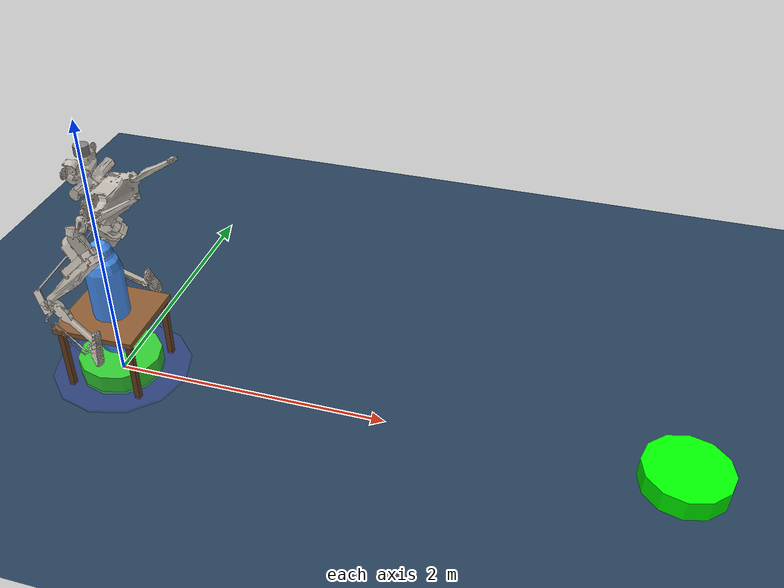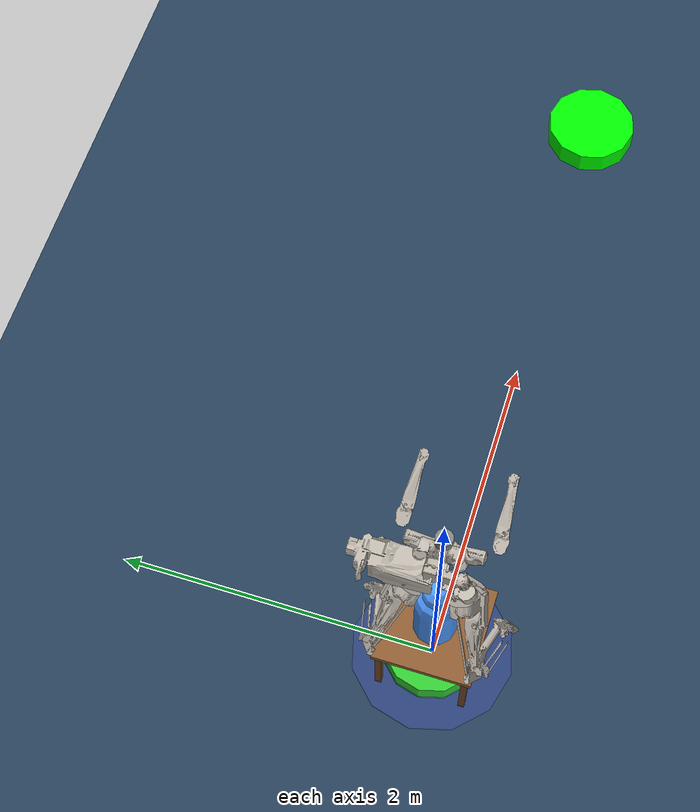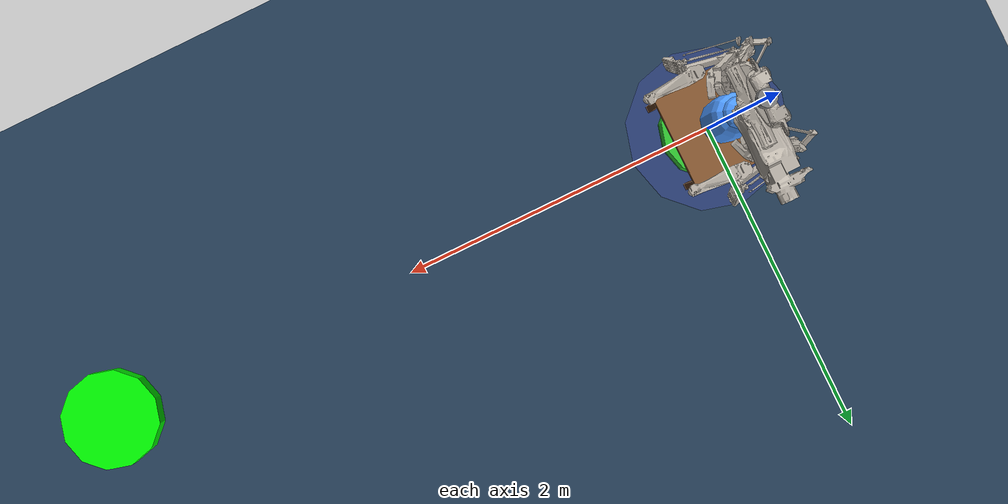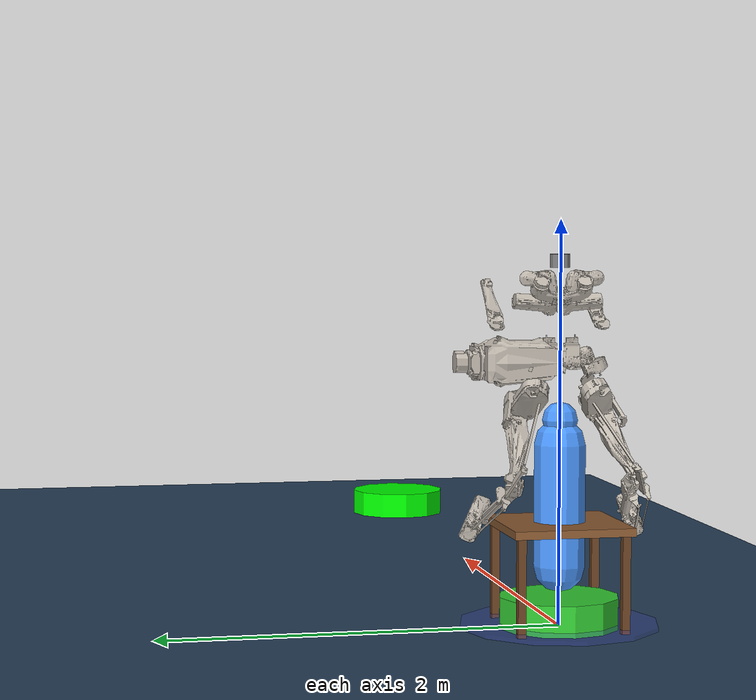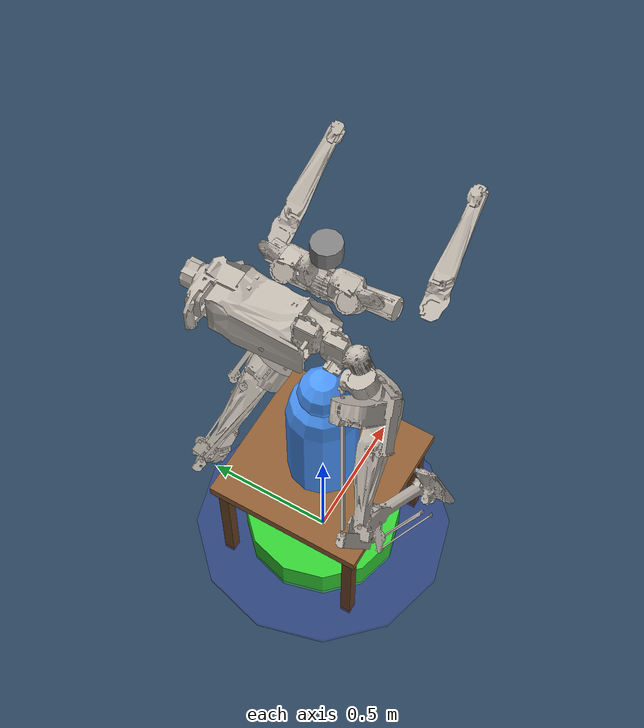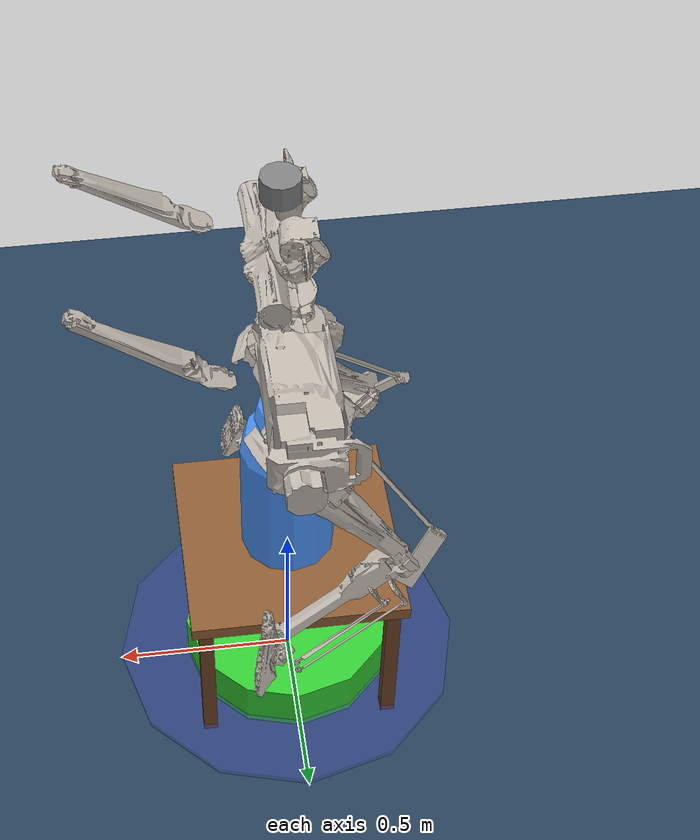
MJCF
<mujoco model='digit-v3'>
  <compiler angle='degree' eulerseq='xyz' meshdir="obj" texturedir="obj"/>
  <option iterations='50' solver='Newton' timestep='0.0005' gravity='0 0 -9.806'/>
  <size nconmax='100' />

  <statistic center="0 0 0.55" extent="1.1"/>

  <visual>
    <headlight diffuse="0.6 0.6 0.6"  ambient="0.3 0.3 0.3" specular="0 0 0"/>
    <rgba haze="0.15 0.25 0.35 1"/>
    <!--global azimuth="-150" elevation="-20"/-->
  </visual>

  <asset>
    <material name="red" rgba="1 0 0 1"/>
    <texture type="skybox" builtin="gradient" rgb1="0.3 0.5 0.7" rgb2="0 0 0" width="512" height="3072"/>
    <texture type="2d" name="groundplane" builtin="checker" mark="edge" rgb1="0.2 0.3 0.4" rgb2="0.1 0.2 0.3" markrgb="0.8 0.8 0.8" width="300" height="300"/>
    <material name="groundplane" texture="groundplane" texuniform="true" texrepeat="2.5 2.5" reflectance="0.2"/>

    <material name='collision' rgba='0.1 0.5 0.9 0.4'/>
    <material name='plane' reflectance='0.000000' texrepeat='1 1' texture='plane' texuniform='true' />
    <material name='robot' rgba='0.9 0.5 0.1 1'/>
    <texture builtin='checker' height='512' name='plane' rgb1='0.9 0.9 0.9' rgb2='0.3 0.3 0.3' type='2d' width='512'/>
    <texture builtin='gradient' height='128' rgb1='0.4 0.6 0.8' rgb2='0 0 0' type='skybox' width='128'/>

    <material name="amazonbody"  texuniform="true"  texture="amazonbody"/>
    <texture type="2d" name="amazonbody" file="amazon.png"/>
    <mesh name='amazonbody' scale='1 1 1' file='amazon_box.obj'/>

    <material name="tablebody"  texuniform="true"  texture="tablebody"/>
    <texture type="2d" name="tablebody" file="table.png"/>
    <mesh name='tablebody' scale='1 1 1' file='table.obj'/>

    <material name="base-0" texture="base-0"/>
    <material name="base-1" texture="base-1"/>
    <material name="base-2" texture="base-2"/>
    <material name="base-3" texture="base-3"/>
    <material name="base-4" texture="base-4"/>
    <material name="left-hip-roll-0" texture="left-hip-roll-0"/>
    <material name="left-hip-yaw-0" texture="left-hip-yaw-0"/>
    <material name="left-hip-pitch-0" texture="left-hip-pitch-0"/>
    <material name="left-achilles-rod-0" texture="left-achilles-rod-0"/>
    <material name="left-knee-0" texture="left-knee-0"/>
    <material name="left-shin-0" texture="left-shin-0"/>
    <material name="left-tarsus-0" texture="left-tarsus-0"/>
    <material name="left-heel-spring-0" texture="left-heel-spring-0"/>
    <material name="left-toe-A-0" texture="left-toe-A-0"/>
    <material name="left-toe-A-rod-0" texture="left-toe-A-rod-0"/>
    <material name="left-toe-B-0" texture="left-toe-B-0"/>
    <material name="left-toe-B-rod-0" texture="left-toe-B-rod-0"/>
    <material name="left-toe-pitch-0" texture="left-toe-pitch-0"/>
    <material name="left-toe-roll-0" texture="left-toe-roll-0"/>
    <material name="left-shoulder-roll-0" texture="left-shoulder-roll-0"/>
    <material name="left-shoulder-pitch-0" texture="left-shoulder-pitch-0"/>
    <material name="left-shoulder-yaw-0" texture="left-shoulder-yaw-0"/>
    <material name="left-elbow-0" texture="left-elbow-0"/>
    <material name="right-hip-roll-0" texture="right-hip-roll-0"/>
    <material name="right-hip-yaw-0" texture="right-hip-yaw-0"/>
    <material name="right-hip-pitch-0" texture="right-hip-pitch-0"/>
    <material name="right-achilles-rod-0" texture="right-achilles-rod-0"/>
    <material name="right-knee-0" texture="right-knee-0"/>
    <material name="right-shin-0" texture="right-shin-0"/>
    <material name="right-tarsus-0" texture="right-tarsus-0"/>
    <material name="right-heel-spring-0" texture="right-heel-spring-0"/>
    <material name="right-toe-A-0" texture="right-toe-A-0"/>
    <material name="right-toe-A-rod-0" texture="right-toe-A-rod-0"/>
    <material name="right-toe-B-0" texture="right-toe-B-0"/>
    <material name="right-toe-B-rod-0" texture="right-toe-B-rod-0"/>
    <material name="right-toe-pitch-0" texture="right-toe-pitch-0"/>
    <material name="right-toe-roll-0" texture="right-toe-roll-0"/>
    <material name="right-shoulder-roll-0" texture="right-shoulder-roll-0"/>
    <material name="right-shoulder-pitch-0" texture="right-shoulder-pitch-0"/>
    <material name="right-shoulder-yaw-0" texture="right-shoulder-yaw-0"/>
    <material name="right-elbow-0" texture="right-elbow-0"/>

    <texture type="2d" name="base-0" file="shin.png"/>
    <texture type="2d" name="base-1" file="hip-roll-housing.png"/>
    <texture type="2d" name="base-2" file="hip-roll-housing.png"/>
    <texture type="2d" name="base-3" file="shoulder-roll-housing.png"/>
    <texture type="2d" name="base-4" file="shoulder-roll-housing.png"/>
    <texture type="2d" name="left-hip-roll-0" file="hip-yaw-housing.png"/>
    <texture type="2d" name="left-hip-yaw-0" file="hip-pitch-housing.png"/>
    <texture type="2d" name="left-hip-pitch-0" file="hip-pitch.png"/>
    <texture type="2d" name="left-achilles-rod-0" file="achilles-rod.png"/>
    <texture type="2d" name="left-knee-0" file="knee.png"/>
    <texture type="2d" name="left-shin-0" file="shin.png"/>
    <texture type="2d" name="left-tarsus-0" file="tarsus.png"/>
    <texture type="2d" name="left-heel-spring-0" file="heel-spring.png"/>
    <texture type="2d" name="left-toe-A-0" file="toe-output.png"/>
    <texture type="2d" name="left-toe-A-rod-0" file="toe-A-rod.png"/>
    <texture type="2d" name="left-toe-B-0" file="toe-output.png"/>
    <texture type="2d" name="left-toe-B-rod-0" file="toe-B-rod.png"/>
    <texture type="2d" name="left-toe-pitch-0" file="toe-pitch.png"/>
    <texture type="2d" name="left-toe-roll-0" file="toe-roll.png"/>
    <texture type="2d" name="left-shoulder-roll-0" file="arm-L1.png"/>
    <texture type="2d" name="left-shoulder-pitch-0" file="arm-L2.png"/>
    <texture type="2d" name="left-shoulder-yaw-0" file="arm-L3.png"/>
    <texture type="2d" name="left-elbow-0" file="arm-L4.png"/>
    <texture type="2d" name="right-hip-roll-0" file="hip-yaw-housing.png"/>
    <texture type="2d" name="right-hip-yaw-0" file="hip-pitch-housing.png"/>
    <texture type="2d" name="right-hip-pitch-0" file="hip-pitch.png"/>
    <texture type="2d" name="right-achilles-rod-0" file="achilles-rod.png"/>
    <texture type="2d" name="right-knee-0" file="knee.png"/>
    <texture type="2d" name="right-shin-0" file="shin.png"/>
    <texture type="2d" name="right-tarsus-0" file="tarsus.png"/>
    <texture type="2d" name="right-heel-spring-0" file="heel-spring.png"/>
    <texture type="2d" name="right-toe-A-0" file="toe-output.png"/>
    <texture type="2d" name="right-toe-A-rod-0" file="toe-A-rod.png"/>
    <texture type="2d" name="right-toe-B-0" file="toe-output.png"/>
    <texture type="2d" name="right-toe-B-rod-0" file="toe-B-rod.png"/>
    <texture type="2d" name="right-toe-pitch-0" file="toe-pitch.png"/>
    <texture type="2d" name="right-toe-roll-0" file="toe-roll.png"/>
    <texture type="2d" name="right-shoulder-roll-0" file="arm-L1.png"/>
    <texture type="2d" name="right-shoulder-pitch-0" file="arm-L2.png"/>
    <texture type="2d" name="right-shoulder-yaw-0" file="arm-L3.png"/>
    <texture type="2d" name="right-elbow-0" file="arm-L4.png"/>

    <mesh name='base-0' file='torso.obj'/>
    <mesh name='base-1' file='hip-roll-housing.obj'/>
    <mesh name='base-2' scale='1 -1 1' file='hip-roll-housing.obj'/>
    <mesh name='base-3' file='shoulder-roll-housing.obj'/>
    <mesh name='base-4' scale='1 -1 1' file='shoulder-roll-housing.obj'/>
    <mesh name='left-hip-roll-0' file='hip-yaw-housing.obj'/>
    <mesh name='left-hip-yaw-0' file='hip-pitch-housing.obj'/>
    <mesh name='left-hip-pitch-0' file='hip-pitch.obj'/>
    <mesh name='left-achilles-rod-0' file='achilles-rod.obj'/>
    <mesh name='left-knee-0' file='knee.obj'/>
    <mesh name='left-shin-0' file='shin.obj'/>
    <mesh name='left-tarsus-0' file='tarsus.obj'/>
    <mesh name='left-heel-spring-0' file='heel-spring.obj'/>
    <mesh name='left-toe-A-0' file='toe-output.obj'/>
    <mesh name='left-toe-A-rod-0' file='toe-A-rod.obj'/>
    <mesh name='left-toe-B-0' file='toe-output.obj'/>
    <mesh name='left-toe-B-rod-0' file='toe-B-rod.obj'/>
    <mesh name='left-toe-pitch-0' file='toe-pitch.obj'/>
    <mesh name='left-toe-roll-0' file='toe-roll.obj'/>
    <mesh name='left-shoulder-roll-0' file='arm-L1.obj'/>
    <mesh name='left-shoulder-pitch-0' file='arm-L2.obj'/>
    <mesh name='left-shoulder-yaw-0' file='arm-L3.obj'/>
    <mesh name='left-elbow-0' file='arm-L4.obj'/>
    <mesh name='right-hip-roll-0' scale='1 -1 1' file='hip-yaw-housing.obj'/>
    <mesh name='right-hip-yaw-0' scale='1 -1 1' file='hip-pitch-housing.obj'/>
    <mesh name='right-hip-pitch-0' scale='1 -1 1' file='hip-pitch.obj'/>
    <mesh name='right-achilles-rod-0' scale='1 -1 1' file='achilles-rod.obj'/>
    <mesh name='right-knee-0' scale='1 -1 1' file='knee.obj'/>
    <mesh name='right-shin-0' scale='1 -1 1' file='shin.obj'/>
    <mesh name='right-tarsus-0' scale='1 -1 1' file='tarsus.obj'/>
    <mesh name='right-heel-spring-0' scale='1 -1 1' file='heel-spring.obj'/>
    <mesh name='right-toe-A-0' scale='1 -1 1' file='toe-output.obj'/>
    <mesh name='right-toe-A-rod-0' scale='1 -1 1' file='toe-A-rod.obj'/>
    <mesh name='right-toe-B-0' scale='1 -1 1' file='toe-output.obj'/>
    <mesh name='right-toe-B-rod-0' scale='1 -1 1' file='toe-B-rod.obj'/>
    <mesh name='right-toe-pitch-0' scale='1 -1 1' file='toe-pitch.obj'/>
    <mesh name='right-toe-roll-0' scale='1 -1 1' file='toe-roll.obj'/>
    <mesh name='right-shoulder-roll-0' scale='1 -1 1' file='arm-L1.obj'/>
    <mesh name='right-shoulder-pitch-0' scale='1 -1 1' file='arm-L2.obj'/>
    <mesh name='right-shoulder-yaw-0' scale='1 -1 1' file='arm-L3.obj'/>
    <mesh name='right-elbow-0' scale='1 -1 1' file='arm-L4.obj'/>

    <hfield name='hf1' file= '../terrains/terrain_n38_w087_1arc_v2.png' nrow='0' ncol='0' size="50 50 0.3 .1"/>

  </asset>
  <default>
    <default class='collision'>
      <geom conaffinity='1' condim='3' contype='1'/>
    </default>
    <equality solimp='0.9 0.95 0.001 0.1 2' solref='0.001 1.1' />
    <geom conaffinity='0' condim='1' contype='0' solref='0.005 1' />
    <joint solreflimit='0.001 1' />
  </default>

  <worldbody>
    <light pos="0 0 3" dir="0 0 -1"  directional="true"/>
    <geom name="floor" size="0 0 .125" type="plane" material="groundplane" conaffinity="15" condim="3" friction='1.0 0.005 0.0001' pos='0 0 0' priority='100'/>

    <body name='base' pos='0.0 0 1.31' euler='-0 0 -0'>
      <camera name="front" pos="15 0 4.5" xyaxes="0 1 0 -1 0 2" mode="trackcom"/>
      <camera name="side" pos="0 -15 4.5" xyaxes="1 0 0 0 1 2" mode="trackcom"/>
      <camera name="back" pos="-15 0 4.5" xyaxes="0 -1 0 1 0 2" mode="trackcom"/>
      <inertial pos='0.001637 0.0002 0.259307' mass='15.028392' fullinertia='0.375905 0.344193 0.098732 -8.8e-05 0.0085 6.6e-05' />
      <joint name="base" type='free' limited='false'/>
      <geom type='mesh' mesh='base-0' pos='0 0 0' euler='-0 0 -0' material='base-0'/>
      <geom type='mesh' mesh='base-1' pos='-0.001 0.091 0' euler='0 -90 0' material='base-1'/>
      <geom type='mesh' mesh='base-2' pos='-0.001 -0.091 0' euler='0 -90 0' material='base-2'/>
      <geom type='mesh' mesh='base-3' pos='-0.001 0.12 0.4' euler='-10 -90 0' material='base-3'/>
      <geom type='mesh' mesh='base-4' pos='-0.001 -0.12 0.4' euler='10 -90 0' material='base-4'/>
      <geom type='box' size='0.0975 0.087 0.245' pos='0.008 0 0.21' euler='-0 0 -0' friction='0.7 0.01 0.005'  mass='15.028392' rgba="0 0 0 0.0" class='collision'/>
      <geom type='cylinder' size='0.05 0.0325' pos='0.02 0 0.49' euler='-0 0 -0' friction='0.7 0.01 0.005'  mass='15.028392' class='collision'/>
      <body name='left-hip-roll' pos='-0.001 0.091 0' euler='21.5 -90 0'>
        <inertial pos='-0.001967 0.000244 0.031435' mass='0.915088' fullinertia='0.001017 0.001148 0.000766 -3e-06 1.3e-05 -4e-06' />
        <joint name='left-hip-roll' type='hinge' axis='0 0 1' range='-60 60' stiffness='0' frictionloss='1' damping='1' armature='0.173824' limited='true' pos='0 0 0'/>
        <geom type='mesh' mesh='left-hip-roll-0' pos='0 0 0' euler='-0 0 -0' material='left-hip-roll-0'/>
        <body name='left-hip-yaw' pos='-0.0505 0 0.044' euler='0 -90 0'>base
          <inertial pos='1e-05 -0.001945 0.042033' mass='0.818753' fullinertia='0.001627 0.001929 0.00077 -1e-06 2e-06 5.3e-05' />
          <joint name='left-hip-yaw' type='hinge' axis='0 0 1' range='-40 40' stiffness='0' frictionloss='1' damping='1' armature='0.0679' limited='true' pos='0 0 0'/>
          <geom type='mesh' mesh='left-hip-yaw-0' pos='0 0 0' euler='-0 0 -0' material='left-hip-yaw-0'/>
          <body name='left-hip-pitch' pos='0 0.004 0.068' euler='90 0 135'>
            <inertial pos='0.060537 0.000521 -0.038857' mass='6.244279' fullinertia='0.011533 0.033345 0.033958 -0.000171 0.000148 0.000178' />
            <joint name='left-hip-pitch' type='hinge' axis='0 0 -1' range='-60 90' stiffness='0' frictionloss='0.5' damping='1' armature='0.120473' limited='true' pos='0 0 0'/>
            <geom type='mesh' mesh='left-hip-pitch-0' pos='0 0 0' euler='-0 0 -0' material='left-hip-pitch-0'/>
            <geom type='cylinder' size='0.05 0.072' pos='0 0 -0.04' euler='-0 0 -0' friction='0.7 0.01 0.005' contype='4' conaffinity='3' mass='6.244279' rgba="0 0 0 0.0" class='collision'/>
            <geom type='cylinder' size='0.05 0.072' pos='0.12 0 -0.04' euler='-0 0 -0' friction='0.7 0.01 0.005' contype='4' conaffinity='3' mass='6.244279' rgba="0 0 0 0.0" class='collision'/>
            <geom type='box' size='0.06 0.05 0.072' pos='0.06 0 -0.04' euler='-0 0 -0' friction='0.7 0.01 0.005' contype='4' conaffinity='3' mass='6.244279' rgba="0 0 0 0.0" class='collision'/>
            <body name='left-achilles-rod' pos='0 0 0.046' euler='4.09 0.05 -82.27'>
              <inertial pos='0.2506 0 0' mass='0.178148' fullinertia='3e-06 0.004501 0.004501 0 0 0' />
              <joint name='left-achilles-rod' type='ball' axis='0 0 1'  stiffness='0' frictionloss='0' damping='0.01' armature='0' limited='false' pos='0 0 0'/>
              <geom type='mesh' mesh='left-achilles-rod-0' pos='0 0 0' euler='-0 0 -0' material='left-achilles-rod-0'/>
              <geom type='capsule' size='0.007 0.25' pos='0.25 0 0' euler='4 90 0' friction='0.7 0.01 0.005' contype='4' conaffinity='3' mass='0.178148' rgba="0 0 0 0.0" class='collision'/>
            </body>
            <body name='left-knee' pos='0.12 0 0.0045' euler='0 0 -90'>
              <inertial pos='0.045641 0.042154 0.001657' mass='1.227077' fullinertia='0.002643 0.005098 0.007019 -0.001832 6.6e-05 4.5e-05' />
              <joint name='left-knee' type='hinge' axis='0 0 1' range='-80 58.4' stiffness='0' frictionloss='0.5' damping='1' armature='0.120473' limited='true' pos='0 0 0'/>
              <geom type='mesh' mesh='left-knee-0' pos='0 0 0' euler='-0 0 -0' material='left-knee-0'/>
              <body name='left-shin' pos='0.060677 0.047406 0' euler='-0 0 -0'>
                <inertial pos='0.174265 0.010265 0.00107' mass='0.895793' fullinertia='0.001128 0.022492 0.022793 0.001098 0.000196 -3e-06' />
                <joint name='left-shin' type='hinge' axis='0 0 1'  stiffness='6000' frictionloss='0' damping='0' armature='0' limited='false' pos='0 0 0'/>
                <geom type='mesh' mesh='left-shin-0' pos='0 0 0' euler='-0 0 -0' material='left-shin-0'/>
                <geom type='cylinder' size='0.03 0.1715' pos='0.23 0 0' euler='0 90 0' friction='0.7 0.01 0.005' contype='4' conaffinity='3' mass='0.895793' rgba="0 0 0 0.0" class='collision'/>
                <geom type='cylinder' size='0.05 0.1' pos='0.125 0.009 0' euler='90 84 -3.042764221e-14' friction='0.7 0.01 0.005' contype='4' conaffinity='3' mass='0.895793' rgba="0 0 0 0.0" class='collision'/>
                <body name='left-tarsus' pos='0.434759 0.02 0' euler='-0 0 103'>
                  <inertial pos='0.100777 -0.029183 0.000678' mass='1.322865' fullinertia='0.000932 0.016409 0.016501 0.00061 0.000102 9e-06' />
                  <joint name='left-tarsus' type='hinge' axis='0 0 1' range='-50.3 71.6' stiffness='0' frictionloss='0' damping='0' armature='0' limited='true' pos='0 0 0'/>
                  <geom type='mesh' mesh='left-tarsus-0' pos='0 0 0' euler='-0 0 -0' material='left-tarsus-0'/>
                  <geom type='capsule' size='0.02 0.18' pos='0.21 -0.03 0' euler='0 90 0' friction='0.7 0.01 0.005' contype='4' conaffinity='3' mass='1.322865' rgba="0 0 0 0.0" class='collision'/>
                  <geom type='box' size='0.007 0.07 0.03' pos='-0.07 -0.012 0' euler='5 3.975693352e-16 65' friction='0.7 0.01 0.005' contype='4' conaffinity='3' mass='1.322865' rgba="0 0 0 0.0" class='collision'/>
                  <body name='left-heel-spring' pos='-0.01766 -0.029456 0.00104' euler='4.47 0.32 155.8'>
                    <inertial pos='0.049086 0.004739 -4.5e-05' mass='0.230018' fullinertia='5.5e-05 0.00074 0.000701 1.5e-05 1e-06 0' />
                    <joint name='left-heel-spring' type='hinge' axis='0 0 1' range='-6 6' stiffness='4375' frictionloss='0' damping='0' armature='0' limited='true' pos='0 0 0'/>
                    <geom type='mesh' mesh='left-heel-spring-0' pos='0 0 0' euler='-0 0 -0' material='left-heel-spring-0'/>
                  </body>
                  <body name='left-toe-A' pos='0.059 -0.034 -0.0276' euler='-180 0 88.96'>
                    <inertial pos='0.005161 1e-06 -0.002248' mass='0.139557' fullinertia='2.9e-05 5.8e-05 7.4e-05 0 -4e-06 0' />
                    <joint name='left-toe-A' type='hinge' axis='0 0 1' range='-46.2755 44.9815' stiffness='0' frictionloss='1' damping='1' armature='0.036089' limited='true' pos='0 0 0'/>
                    <geom type='mesh' mesh='left-toe-A-0' pos='0 0 0' euler='-0 0 -0' material='left-toe-A-0'/>
                    <body name='left-toe-A-rod' pos='0.057 0 -0.008' euler='0.34 2.14 -88.45'>
                      <inertial pos='0.171071 0 0' mass='0.090983' fullinertia='1e-06 0.001182 0.001182 0 0 0' />
                      <joint name='left-toe-A-rod' type='ball' axis='0 0 1'  stiffness='0' frictionloss='0' damping='0.01' armature='0' limited='false' pos='0 0 0'/>
                      <geom type='mesh' mesh='left-toe-A-rod-0' pos='0 0 0' euler='-0 0 -0' material='left-toe-A-rod-0'/>
                      <geom type='capsule' size='0.007 0.17' pos='0.17 0 0' euler='4 90 0' friction='0.7 0.01 0.005' contype='4' conaffinity='3' mass='0.090983' rgba="0 0 0 0.0" class='collision'/>
                    </body>
                  </body>
                  <body name='left-toe-B' pos='0.111 -0.034 0.0276' euler='0 0 -88.96'>
                    <inertial pos='0.005161 1e-06 -0.002248' mass='0.139557' fullinertia='2.9e-05 5.8e-05 7.4e-05 0 -4e-06 0' />
                    <joint name='left-toe-B' type='hinge' axis='0 0 1' range='-45.8918 45.5476' stiffness='0' frictionloss='1' damping='1' armature='0.036089' limited='true' pos='0 0 0'/>
                    <geom type='mesh' mesh='left-toe-B-0' pos='0 0 0' euler='-0 0 -0' material='left-toe-B-0'/>
                    <body name='left-toe-B-rod' pos='0.057 0 -0.008' euler='-0.22 -3.08 88.34'>
                      <inertial pos='0.142991 0 0' mass='0.079507' fullinertia='1e-06 0.000768 0.000768 0 0 0' />
                      <joint name='left-toe-B-rod' type='ball' axis='0 0 1'  stiffness='0' frictionloss='0' damping='0.01' armature='0' limited='false' pos='0 0 0'/>
                      <geom type='mesh' mesh='left-toe-B-rod-0' pos='0 0 0' euler='-0 0 -0' material='left-toe-B-rod-0'/>
                      <geom type='capsule' size='0.007 0.144' pos='0.144 0 0' euler='4 90 0' friction='0.7 0.01 0.005' contype='4' conaffinity='3' mass='0.079507' rgba="0 0 0 0.0" class='collision'/>
                    </body>
                  </body>
                  <body name='left-toe-pitch' pos='0.408 -0.04 0' euler='-0 0 71.75'>
                    <inertial pos='-0.000141 2e-06 3e-06' mass='0.043881' fullinertia='5e-06 8e-06 4e-06 0 0 0' />
                    <joint name='left-toe-pitch' type='hinge' axis='0 0 1' range='-44 34' stiffness='0' frictionloss='0' damping='0' armature='0' limited='true' pos='0 0 0'/>
                    <geom type='mesh' mesh='left-toe-pitch-0' pos='0 0 0' euler='-0 0 -0' material='left-toe-pitch-0'/>
                    <body name='left-toe-roll' pos='0 0 0' euler='0 90 0'>
                      <inertial pos='9e-06 -0.028084 -0.023204' mass='0.531283' fullinertia='0.00187 0.001616 0.000843 0 0 0.000566' />
                      <joint name='left-toe-roll' type='hinge' axis='0 0 1' range='-37 33' stiffness='0' frictionloss='0' damping='0' armature='0' limited='true' pos='0 0 0'/>
                      <geom type='mesh' mesh='left-toe-roll-0' pos='0 0 0' euler='-0 0 -0' material='left-toe-roll-0'/>
                      <geom name='left-foot' type='box' size='0.04 0.1175 0.0115' pos='0 -0.0437 -0.0255' euler='-60 0 0' friction='0.7 0.01 0.005' contype='4' conaffinity='3' mass='0.531283' rgba="0 0 0 0.0" class='collision'/>
                      <body name='left-foot' pos='0 -0.05456 -0.0315' euler='-60 0 -90'>
                      </body>
                    </body>
                  </body>
                </body>
              </body>
            </body>
          </body>
        </body>
      </body>
      <body name='left-shoulder-roll' pos='-0.001 0.12 0.4' euler='-10 -90 0'>
        <inertial pos='-0.000819 -0.003158 0.023405' mass='0.535396' fullinertia='0.000704 0.00075 0.000298 1.4e-05 1.2e-05 3.5e-05' />
        <joint name='left-shoulder-roll' type='hinge' axis='0 0 1' range='-75 75' stiffness='0' frictionloss='2' damping='2' armature='0.173824' limited='true' pos='0 0 0'/>
        <geom type='mesh' mesh='left-shoulder-roll-0' pos='0 0 0' euler='0 0 -16' material='left-shoulder-roll-0'/>
        <body name='left-shoulder-pitch' pos='-0.00317 -0.011055 0.0555' euler='90 -16 -45'>
          <inertial pos='-4.2e-05 -0.061882 -0.073788' mass='1.440357' fullinertia='0.006761 0.002087 0.005778 -6e-06 -3e-06 -0.002046' />
          <joint name='left-shoulder-pitch' type='hinge' axis='0 0 -1' range='-145 145' stiffness='0' frictionloss='2' damping='2' armature='0.173824' limited='true' pos='0 0 0'/>
          <geom type='mesh' mesh='left-shoulder-pitch-0' pos='0 0 0' euler='-0 0 -0' material='left-shoulder-pitch-0'/>
          <geom type='cylinder' size='0.038 0.07' pos='0 -0.093 -0.1' euler='90 0 -0' friction='0.7 0.01 0.005'  mass='1.440357' rgba="0 0 0 0.0" class='collision'/>
          <body name='left-shoulder-yaw' pos='0 -0.165 -0.1' euler='90 0 -0'>
            <inertial pos='-3e-05 0.001937 0.11407' mass='1.065387' fullinertia='0.006967 0.007003 0.000673 -1e-06 -1e-06 -1.5e-05' />
            <joint name='left-shoulder-yaw' type='hinge' axis='0 0 1' range='-100 100' stiffness='0' frictionloss='2' damping='1' armature='0.0679' limited='true' pos='0 0 0'/>
            <geom type='mesh' mesh='left-shoulder-yaw-0' pos='0 0 0' euler='-0 0 -0' material='left-shoulder-yaw-0'/>
            <geom type='cylinder' size='0.038 0.0675' pos='0 0 0.092558' euler='-0 0 -0' friction='0.7 0.01 0.005'  mass='1.065387' rgba="0 0 0 0.0" class='collision'/>
            <geom type='cylinder' size='0.03 0.04' pos='0 0.0035 0.185' euler='90 1.590277341e-15 22.5' friction='0.7 0.01 0.005'  mass='1.065387' rgba="0 0 0 0.0" class='collision'/>
            <body name='left-elbow' pos='0 -0.0385 0.185' euler='90 1.590277341e-15 22.5'>
              <inertial pos='0.107996 0.000521 -0.017765' mass='0.550582' fullinertia='0.000476 0.009564 0.009437 -2.9e-05 0.001403 9e-06' />
              <joint name='left-elbow' type='hinge' axis='0 0 1' range='-77.5 77.5' stiffness='0' frictionloss='2' damping='1' armature='0.173824' limited='true' pos='0 0 0'/>
              <geom type='mesh' mesh='left-elbow-0' pos='0 0 0' euler='-0 0 -0' material='left-elbow-0'/>
              <geom type='cylinder' size='0.013 0.1565' pos='0.184 0.01 -0.026' euler='170 78 -180' friction='0.7 0.01 0.005'  mass='0.550582' rgba="0 0 0 0.0" class='collision'/>
              <geom type='sphere' size='0.015' pos='0.37937 0 -0.061912' euler='-0 0 -0' friction='0.7 0.01 0.005'  mass='0.550582' rgba="0 0 0 0.0" class='collision'/>
              <body name='left-hand' pos='0.369 0 -0.07912' euler='90 0 -10'>
              </body>
            </body>
          </body>
        </body>
      </body>
      <body name='right-hip-roll' pos='-0.001 -0.091 0' euler='-21.5 -90 0'>
        <inertial pos='-0.001967 -0.000244 0.031435' mass='0.915088' fullinertia='0.001017 0.001148 0.000766 3e-06 1.3e-05 4e-06' />
        <joint name='right-hip-roll' type='hinge' axis='0 0 1' range='-60 60' stiffness='0' frictionloss='1' damping='1' armature='0.173824' limited='true' pos='0 0 0'/>
        <geom type='mesh' mesh='right-hip-roll-0' pos='0 0 0' euler='-0 0 -0' material='right-hip-roll-0'/>
        <body name='right-hip-yaw' pos='-0.0505 0 0.044' euler='0 -90 0'>
          <inertial pos='1e-05 0.001945 0.042033' mass='0.818753' fullinertia='0.001627 0.001929 0.00077 1e-06 2e-06 -5.3e-05' />
          <joint name='right-hip-yaw' type='hinge' axis='0 0 1' range='-40 40' stiffness='0' frictionloss='1' damping='1' armature='0.0679' limited='true' pos='0 0 0'/>
          <geom type='mesh' mesh='right-hip-yaw-0' pos='0 0 0' euler='-0 0 -0' material='right-hip-yaw-0'/>
          <body name='right-hip-pitch' pos='0 -0.004 0.068' euler='-90 0 -135'>
            <inertial pos='0.060537 -0.000521 -0.038857' mass='6.244279' fullinertia='0.011533 0.033345 0.033958 0.000171 0.000148 -0.000178' />
            <joint name='right-hip-pitch' type='hinge' axis='0 0 -1' range='-90 60' stiffness='0' frictionloss='0.5' damping='1' armature='0.120473' limited='true' pos='0 0 0'/>
            <geom type='mesh' mesh='right-hip-pitch-0' pos='0 0 0' euler='-0 0 -0' material='right-hip-pitch-0'/>
            <geom type='cylinder' size='0.05 0.072' pos='0 0 -0.04' euler='-0 0 -0' friction='0.7 0.01 0.005' contype='2' conaffinity='1' mass='6.244279' rgba="0 0 0 0.0" class='collision'/>
            <geom type='cylinder' size='0.05 0.072' pos='0.12 0 -0.04' euler='-0 0 -0' friction='0.7 0.01 0.005' contype='2' conaffinity='1' mass='6.244279' rgba="0 0 0 0.0" class='collision'/>
            <geom type='box' size='0.06 0.05 0.072' pos='0.06 0 -0.04' euler='-0 0 -0' friction='0.7 0.01 0.005' contype='2' conaffinity='1' mass='6.244279' rgba="0 0 0 0.0" class='collision'/>
            <body name='right-achilles-rod' pos='0 0 0.046' euler='-4.09 0.05 82.27'>
              <inertial pos='0.2506 0 0' mass='0.178148' fullinertia='3e-06 0.004501 0.004501 0 0 0' />
              <joint name='right-achilles-rod' type='ball' axis='0 0 1'  stiffness='0' frictionloss='0' damping='0.01' armature='0' limited='false' pos='0 0 0'/>
              <geom type='mesh' mesh='right-achilles-rod-0' pos='0 0 0' euler='-0 0 -0' material='right-achilles-rod-0'/>
              <geom type='capsule' size='0.007 0.25' pos='0.25 0 0' euler='-4 90 0' friction='0.7 0.01 0.005' contype='2' conaffinity='1' mass='0.178148' rgba="0 0 0 0.0" class='collision'/>
            </body>
            <body name='right-knee' pos='0.12 0 0.0045' euler='-0 0 90'>
              <inertial pos='0.045641 -0.042154 0.001657' mass='1.227077' fullinertia='0.002643 0.005098 0.007019 0.001832 6.6e-05 -4.5e-05' />
              <joint name='right-knee' type='hinge' axis='0 0 1' range='-58.4 80' stiffness='0' frictionloss='0.5' damping='1' armature='0.120473' limited='true' pos='0 0 0'/>
              <geom type='mesh' mesh='right-knee-0' pos='0 0 0' euler='-0 0 -0' material='right-knee-0'/>
              <body name='right-shin' pos='0.060677 -0.047406 0' euler='-0 0 -0'>
                <inertial pos='0.174265 -0.010265 0.00107' mass='0.895793' fullinertia='0.001128 0.022492 0.022793 -0.001098 0.000196 3e-06' />
                <joint name='right-shin' type='hinge' axis='0 0 1'  stiffness='6000' frictionloss='0' damping='0' armature='0' limited='false' pos='0 0 0'/>
                <geom type='mesh' mesh='right-shin-0' pos='0 0 0' euler='-0 0 -0' material='right-shin-0'/>
                <geom type='cylinder' size='0.03 0.1715' pos='0.23 0 0' euler='0 90 0' friction='0.7 0.01 0.005' contype='2' conaffinity='1' mass='0.895793' rgba="0 0 0 0.0" class='collision'/>
                <geom type='cylinder' size='0.05 0.1' pos='0.125 -0.009 0' euler='-90 84 3.042764221e-14' friction='0.7 0.01 0.005' contype='2' conaffinity='1' mass='0.895793' rgba="0 0 0 0.0" class='collision'/>
                <body name='right-tarsus' pos='0.434759 -0.02 0' euler='0 0 -103'>
                  <inertial pos='0.100777 0.029183 0.000678' mass='1.322865' fullinertia='0.000932 0.016409 0.016501 -0.00061 0.000102 -9e-06' />
                  <joint name='right-tarsus' type='hinge' axis='0 0 1' range='-71.6 50.3' stiffness='0' frictionloss='0' damping='0' armature='0' limited='true' pos='0 0 0'/>
                  <geom type='mesh' mesh='right-tarsus-0' pos='0 0 0' euler='-0 0 -0' material='right-tarsus-0'/>
                  <geom type='capsule' size='0.02 0.18' pos='0.21 0.03 0' euler='0 90 0' friction='0.7 0.01 0.005' contype='2' conaffinity='1' mass='1.322865' rgba="0 0 0 0.0" class='collision'/>
                  <geom type='box' size='0.007 0.07 0.03' pos='-0.07 0.012 0' euler='-5 3.975693352e-16 -65' friction='0.7 0.01 0.005' contype='2' conaffinity='1' mass='1.322865' rgba="0 0 0 0.0" class='collision'/>
                  <body name='right-heel-spring' pos='-0.01766 0.029456 0.00104' euler='-4.47 0.32 -155.8'>
                    <inertial pos='0.049086 -0.004739 -4.5e-05' mass='0.230018' fullinertia='5.5e-05 0.00074 0.000701 -1.5e-05 1e-06 0' />
                    <joint name='right-heel-spring' type='hinge' axis='0 0 1' range='-6 6' stiffness='4375' frictionloss='0' damping='0' armature='0' limited='true' pos='0 0 0'/>
                    <geom type='mesh' mesh='right-heel-spring-0' pos='0 0 0' euler='-0 0 -0' material='right-heel-spring-0'/>
                  </body>
                  <body name='right-toe-A' pos='0.059 0.034 -0.0276' euler='180 0 -88.96'>
                    <inertial pos='0.005161 -1e-06 -0.002248' mass='0.139557' fullinertia='2.9e-05 5.8e-05 7.4e-05 0 -4e-06 0' />
                    <joint name='right-toe-A' type='hinge' axis='0 0 1' range='-44.9815 46.2755' stiffness='0' frictionloss='1' damping='1' armature='0.036089' limited='true' pos='0 0 0'/>
                    <geom type='mesh' mesh='right-toe-A-0' pos='0 0 0' euler='-0 0 -0' material='right-toe-A-0'/>
                    <body name='right-toe-A-rod' pos='0.057 0 -0.008' euler='-0.34 2.14 88.45'>
                      <inertial pos='0.171071 0 0' mass='0.090983' fullinertia='1e-06 0.001182 0.001182 0 0 0' />
                      <joint name='right-toe-A-rod' type='ball' axis='0 0 1'  stiffness='0' frictionloss='0' damping='0.01' armature='0' limited='false' pos='0 0 0'/>
                      <geom type='mesh' mesh='right-toe-A-rod-0' pos='0 0 0' euler='-0 0 -0' material='right-toe-A-rod-0'/>
                      <geom type='capsule' size='0.007 0.17' pos='0.17 0 0' euler='-4 90 0' friction='0.7 0.01 0.005' contype='2' conaffinity='1' mass='0.090983' rgba="0 0 0 0.0" class='collision'/>
                    </body>
                  </body>
                  <body name='right-toe-B' pos='0.111 0.034 0.0276' euler='-0 0 88.96'>
                    <inertial pos='0.005161 -1e-06 -0.002248' mass='0.139557' fullinertia='2.9e-05 5.8e-05 7.4e-05 0 -4e-06 0' />
                    <joint name='right-toe-B' type='hinge' axis='0 0 1' range='-45.5476 45.8918' stiffness='0' frictionloss='1' damping='1' armature='0.036089' limited='true' pos='0 0 0'/>
                    <geom type='mesh' mesh='right-toe-B-0' pos='0 0 0' euler='-0 0 -0' material='right-toe-B-0'/>
                    <body name='right-toe-B-rod' pos='0.057 0 -0.008' euler='0.22 -3.08 -88.34'>
                      <inertial pos='0.142991 0 0' mass='0.079507' fullinertia='1e-06 0.000768 0.000768 0 0 0' />
                      <joint name='right-toe-B-rod' type='ball' axis='0 0 1'  stiffness='0' frictionloss='0' damping='0.01' armature='0' limited='false' pos='0 0 0'/>
                      <geom type='mesh' mesh='right-toe-B-rod-0' pos='0 0 0' euler='-0 0 -0' material='right-toe-B-rod-0'/>
                      <geom type='capsule' size='0.007 0.144' pos='0.144 0 0' euler='-4 90 0' friction='0.7 0.01 0.005' contype='2' conaffinity='1' mass='0.079507' rgba="0 0 0 0.0" class='collision'/>
                    </body>
                  </body>
                  <body name='right-toe-pitch' pos='0.408 0.04 0' euler='0 0 -71.75'>
                    <inertial pos='-0.000141 -2e-06 3e-06' mass='0.043881' fullinertia='5e-06 8e-06 4e-06 0 0 0' />
                    <joint name='right-toe-pitch' type='hinge' axis='0 0 1' range='-34 44' stiffness='0' frictionloss='0' damping='0' armature='0' limited='true' pos='0 0 0'/>
                    <geom type='mesh' mesh='right-toe-pitch-0' pos='0 0 0' euler='-0 0 -0' material='right-toe-pitch-0'/>
                    <body name='right-toe-roll' pos='0 0 0' euler='0 90 0'>
                      <inertial pos='9e-06 0.028084 -0.023204' mass='0.531283' fullinertia='0.00187 0.001616 0.000843 0 0 -0.000566' />
                      <joint name='right-toe-roll' type='hinge' axis='0 0 1' range='-33 37' stiffness='0' frictionloss='0' damping='0' armature='0' limited='true' pos='0 0 0'/>
                      <geom type='mesh' mesh='right-toe-roll-0' pos='0 0 0' euler='-0 0 -0' material='right-toe-roll-0'/>
                      <geom name='right-foot' type='box' size='0.04 0.1175 0.0115' pos='0 0.0437 -0.0255' euler='60 0 -0' friction='0.7 0.01 0.005' contype='2' conaffinity='1' mass='0.531283' rgba="0 0 0 0.0" class='collision'/>
                      <body name='right-foot' pos='0 0.05456 -0.0315' euler='60 0 90'>
                      </body>
                    </body>
                  </body>
                </body>
              </body>
            </body>
          </body>
        </body>
      </body>
      <body name='right-shoulder-roll' pos='-0.001 -0.12 0.4' euler='10 -90 0'>
        <inertial pos='-0.000819 0.003158 0.023405' mass='0.535396' fullinertia='0.000704 0.00075 0.000298 -1.4e-05 1.2e-05 -3.5e-05' />
        <joint name='right-shoulder-roll' type='hinge' axis='0 0 1' range='-75 75' stiffness='0' frictionloss='2' damping='2' armature='0.173824' limited='true' pos='0 0 0'/>
        <geom type='mesh' mesh='right-shoulder-roll-0' pos='0 0 0' euler='-0 0 16' material='right-shoulder-roll-0'/>
        <body name='right-shoulder-pitch' pos='-0.00317 0.011055 0.0555' euler='-90 -16 45'>
          <inertial pos='-4.2e-05 0.061882 -0.073788' mass='1.440357' fullinertia='0.006761 0.002087 0.005778 6e-06 -3e-06 0.002046' />
          <joint name='right-shoulder-pitch' type='hinge' axis='0 0 -1' range='-145 145' stiffness='0' frictionloss='2' damping='2' armature='0.173824' limited='true' pos='0 0 0'/>
          <geom type='mesh' mesh='right-shoulder-pitch-0' pos='0 0 0' euler='-0 0 -0' material='right-shoulder-pitch-0'/>
          <geom type='cylinder' size='0.038 0.07' pos='0 0.093 -0.1' euler='-90 0 0' friction='0.7 0.01 0.005'  mass='1.440357' rgba="0 0 0 0.0" class='collision'/>
          <body name='right-shoulder-yaw' pos='0 0.165 -0.1' euler='-90 0 0'>
            <inertial pos='-3e-05 -0.001937 0.11407' mass='1.065387' fullinertia='0.006967 0.007003 0.000673 1e-06 -1e-06 1.5e-05' />
            <joint name='right-shoulder-yaw' type='hinge' axis='0 0 1' range='-100 100' stiffness='0' frictionloss='2' damping='1' armature='0.0679' limited='true' pos='0 0 0'/>
            <geom type='mesh' mesh='right-shoulder-yaw-0' pos='0 0 0' euler='-0 0 -0' material='right-shoulder-yaw-0'/>
            <geom type='cylinder' size='0.038 0.0675' pos='0 0 0.092558' euler='-0 0 -0' friction='0.7 0.01 0.005'  mass='1.065387' rgba="0 0 0 0.0" class='collision'/>
            <geom type='cylinder' size='0.03 0.04' pos='0 -0.0035 0.185' euler='-90 1.590277341e-15 -22.5' friction='0.7 0.01 0.005'  mass='1.065387' rgba="0 0 0 0.0" class='collision'/>
            <body name='right-elbow' pos='0 0.0385 0.185' euler='-90 1.590277341e-15 -22.5'>
              <inertial pos='0.107996 -0.000521 -0.017765' mass='0.550582' fullinertia='0.000476 0.009564 0.009437 2.9e-05 0.001403 -9e-06' />
              <joint name='right-elbow' type='hinge' axis='0 0 1' range='-77.5 77.5' stiffness='0' frictionloss='2' damping='1' armature='0.173824' limited='true' pos='0 0 0'/>
              <geom type='mesh' mesh='right-elbow-0' pos='0 0 0' euler='-0 0 -0' material='right-elbow-0'/>
              <geom type='cylinder' size='0.013 0.1565' pos='0.184 -0.01 -0.026' euler='-170 78 180' friction='0.7 0.01 0.005'  mass='0.550582' rgba="0 0 0 0.0" class='collision'/>
              <geom type='sphere' size='0.015' pos='0.37937 0 -0.061912' euler='-0 0 -0' friction='0.7 0.01 0.005'  mass='0.550582' rgba="0 0 0 0.0" class='collision'/>
              <body name='right-hand' pos='0.369 0 -0.07912' euler='-90 0 10'>
              </body>
            </body>
          </body>
        </body>
      </body>
    </body>
<body name='r2_base' pos='0.0 0 1.31' euler='-0 0 -0'>
      <camera name='r2_front' pos="15 0 4.5" xyaxes="0 1 0 -1 0 2" mode="trackcom"/>
      <camera name='r2_side' pos="0 -15 4.5" xyaxes="1 0 0 0 1 2" mode="trackcom"/>
      <camera name='r2_back' pos="-15 0 4.5" xyaxes="0 -1 0 1 0 2" mode="trackcom"/>
      <inertial pos='0.001637 0.0002 0.259307' mass="0.0015028392" fullinertia="3.75905e-05 3.44193e-05 9.8732e-06 -8.8e-09 8.5e-07 6.6e-09" />
      <joint name='r2_base' type='free' limited='false'/>
      <geom contype="0" conaffinity="0" type='mesh' mesh='base-0' pos='0 0 0' euler='-0 0 -0' material='base-0'/>
      <geom contype="0" conaffinity="0" type='mesh' mesh='base-1' pos='-0.001 0.091 0' euler='0 -90 0' material='base-1'/>
      <geom contype="0" conaffinity="0" type='mesh' mesh='base-2' pos='-0.001 -0.091 0' euler='0 -90 0' material='base-2'/>
      <geom contype="0" conaffinity="0" type='mesh' mesh='base-3' pos='-0.001 0.12 0.4' euler='-10 -90 0' material='base-3'/>
      <geom contype="0" conaffinity="0" type='mesh' mesh='base-4' pos='-0.001 -0.12 0.4' euler='10 -90 0' material='base-4'/>
      <geom contype="0" conaffinity="0" type='box' size='0.0975 0.087 0.245' pos='0.008 0 0.21' euler='-0 0 -0' friction='0.7 0.01 0.005'  mass="0.0015028392" rgba="0 0 0 0.0" class='collision'/>
      <geom contype="0" conaffinity="0" type='cylinder' size='0.05 0.0325' pos='0.02 0 0.49' euler='-0 0 -0' friction='0.7 0.01 0.005'  mass="0.0015028392" class='collision'/>
      <body name='r2_left-hip-roll' pos='-0.001 0.091 0' euler='21.5 -90 0'>
        <inertial pos='-0.001967 0.000244 0.031435' mass="9.15088e-05" fullinertia="1.017e-07 1.148e-07 7.66e-08 -3e-10 1.3e-09 -4e-10" />
        <joint name='r2_left-hip-roll' type='hinge' axis='0 0 1' range='-60 60' stiffness='0' frictionloss='0' damping='0' armature='0' limited='true' pos='0 0 0'/>
        <geom contype="0" conaffinity="0" type='mesh' mesh='left-hip-roll-0' pos='0 0 0' euler='-0 0 -0' material='left-hip-roll-0'/>
        <body name='r2_left-hip-yaw' pos='-0.0505 0 0.044' euler='0 -90 0'>base
          <inertial pos='1e-05 -0.001945 0.042033' mass="8.18753e-05" fullinertia="1.627e-07 1.929e-07 7.7e-08 -1e-10 2e-10 5.3e-09" />
          <joint name='r2_left-hip-yaw' type='hinge' axis='0 0 1' range='-40 40' stiffness='0' frictionloss='0' damping='0' armature='0' limited='true' pos='0 0 0'/>
          <geom contype="0" conaffinity="0" type='mesh' mesh='left-hip-yaw-0' pos='0 0 0' euler='-0 0 -0' material='left-hip-yaw-0'/>
          <body name='r2_left-hip-pitch' pos='0 0.004 0.068' euler='90 0 135'>
            <inertial pos='0.060537 0.000521 -0.038857' mass="0.0006244279" fullinertia="1.1533e-06 3.3345e-06 3.3958e-06 -1.71e-08 1.48e-08 1.78e-08" />
            <joint name='r2_left-hip-pitch' type='hinge' axis='0 0 -1' range='-60 90' stiffness='0' frictionloss='0' damping='0' armature='0' limited='true' pos='0 0 0'/>
            <geom contype="0" conaffinity="0" type='mesh' mesh='left-hip-pitch-0' pos='0 0 0' euler='-0 0 -0' material='left-hip-pitch-0'/>
            <geom contype="0" conaffinity="0" type='cylinder' size='0.05 0.072' pos='0 0 -0.04' euler='-0 0 -0' friction='0.7 0.01 0.005' mass="0.0006244279" rgba="0 0 0 0.0" class='collision'/>
            <geom contype="0" conaffinity="0" type='cylinder' size='0.05 0.072' pos='0.12 0 -0.04' euler='-0 0 -0' friction='0.7 0.01 0.005' mass="0.0006244279" rgba="0 0 0 0.0" class='collision'/>
            <geom contype="0" conaffinity="0" type='box' size='0.06 0.05 0.072' pos='0.06 0 -0.04' euler='-0 0 -0' friction='0.7 0.01 0.005' mass="0.0006244279" rgba="0 0 0 0.0" class='collision'/>
            <body name='r2_left-achilles-rod' pos='0 0 0.046' euler='4.09 0.05 -82.27'>
              <inertial pos='0.2506 0 0' mass="1.78148e-05" fullinertia="3e-10 4.501e-07 4.501e-07 0 0 0" />
              <joint name='r2_left-achilles-rod' type='ball' axis='0 0 1' stiffness='0' frictionloss='0' damping='0' armature='0' limited='false' pos='0 0 0'/>
              <geom contype="0" conaffinity="0" type='mesh' mesh='left-achilles-rod-0' pos='0 0 0' euler='-0 0 -0' material='left-achilles-rod-0'/>
              <geom contype="0" conaffinity="0" type='capsule' size='0.007 0.25' pos='0.25 0 0' euler='4 90 0' friction='0.7 0.01 0.005' mass="1.78148e-05" rgba="0 0 0 0.0" class='collision'/>
            </body>
            <body name='r2_left-knee' pos='0.12 0 0.0045' euler='0 0 -90'>
              <inertial pos='0.045641 0.042154 0.001657' mass="0.0001227077" fullinertia="2.643e-07 5.098e-07 7.019e-07 -1.832e-07 6.6e-09 4.5e-09" />
              <joint name='r2_left-knee' type='hinge' axis='0 0 1' range='-80 58.4' stiffness='0' frictionloss='0' damping='0' armature='0' limited='true' pos='0 0 0'/>
              <geom contype="0" conaffinity="0" type='mesh' mesh='left-knee-0' pos='0 0 0' euler='-0 0 -0' material='left-knee-0'/>
              <body name='r2_left-shin' pos='0.060677 0.047406 0' euler='-0 0 -0'>
                <inertial pos='0.174265 0.010265 0.00107' mass="8.95793e-05" fullinertia="1.128e-07 2.2492e-06 2.2793e-06 1.098e-07 1.96e-08 -3e-10" />
                <joint name='r2_left-shin' type='hinge' axis='0 0 1' stiffness='0' frictionloss='0' damping='0' armature='0' limited='false' pos='0 0 0'/>
                <geom contype="0" conaffinity="0" type='mesh' mesh='left-shin-0' pos='0 0 0' euler='-0 0 -0' material='left-shin-0'/>
                <geom contype="0" conaffinity="0" type='cylinder' size='0.03 0.1715' pos='0.23 0 0' euler='0 90 0' friction='0.7 0.01 0.005' mass="8.95793e-05" rgba="0 0 0 0.0" class='collision'/>
                <geom contype="0" conaffinity="0" type='cylinder' size='0.05 0.1' pos='0.125 0.009 0' euler='90 84 -3.042764221e-14' friction='0.7 0.01 0.005' mass="8.95793e-05" rgba="0 0 0 0.0" class='collision'/>
                <body name='r2_left-tarsus' pos='0.434759 0.02 0' euler='-0 0 103'>
                  <inertial pos='0.100777 -0.029183 0.000678' mass="0.0001322865" fullinertia="9.32e-08 1.6409e-06 1.6501e-06 6.1e-08 1.02e-08 9e-10" />
                  <joint name='r2_left-tarsus' type='hinge' axis='0 0 1' range='-50.3 71.6' stiffness='0' frictionloss='0' damping='0' armature='0' limited='true' pos='0 0 0'/>
                  <geom contype="0" conaffinity="0" type='mesh' mesh='left-tarsus-0' pos='0 0 0' euler='-0 0 -0' material='left-tarsus-0'/>
                  <geom contype="0" conaffinity="0" type='capsule' size='0.02 0.18' pos='0.21 -0.03 0' euler='0 90 0' friction='0.7 0.01 0.005' mass="0.0001322865" rgba="0 0 0 0.0" class='collision'/>
                  <geom contype="0" conaffinity="0" type='box' size='0.007 0.07 0.03' pos='-0.07 -0.012 0' euler='5 3.975693352e-16 65' friction='0.7 0.01 0.005' mass="0.0001322865" rgba="0 0 0 0.0" class='collision'/>
                  <body name='r2_left-heel-spring' pos='-0.01766 -0.029456 0.00104' euler='4.47 0.32 155.8'>
                    <inertial pos='0.049086 0.004739 -4.5e-05' mass="2.30018e-05" fullinertia="5.5e-09 7.4e-08 7.01e-08 1.5e-09 1e-10 0" />
                    <joint name='r2_left-heel-spring' type='hinge' axis='0 0 1' range='-6 6' stiffness='0' frictionloss='0' damping='0' armature='0' limited='true' pos='0 0 0'/>
                    <geom contype="0" conaffinity="0" type='mesh' mesh='left-heel-spring-0' pos='0 0 0' euler='-0 0 -0' material='left-heel-spring-0'/>
                  </body>
                  <body name='r2_left-toe-A' pos='0.059 -0.034 -0.0276' euler='-180 0 88.96'>
                    <inertial pos='0.005161 1e-06 -0.002248' mass="1.39557e-05" fullinertia="2.9e-09 5.8e-09 7.4e-09 0 -4e-10 0" />
                    <joint name='r2_left-toe-A' type='hinge' axis='0 0 1' range='-46.2755 44.9815' stiffness='0' frictionloss='0' damping='0' armature='0' limited='true' pos='0 0 0'/>
                    <geom contype="0" conaffinity="0" type='mesh' mesh='left-toe-A-0' pos='0 0 0' euler='-0 0 -0' material='left-toe-A-0'/>
                    <body name='r2_left-toe-A-rod' pos='0.057 0 -0.008' euler='0.34 2.14 -88.45'>
                      <inertial pos='0.171071 0 0' mass="9.0983e-06" fullinertia="1e-10 1.182e-07 1.182e-07 0 0 0" />
                      <joint name='r2_left-toe-A-rod' type='ball' axis='0 0 1' stiffness='0' frictionloss='0' damping='0' armature='0' limited='false' pos='0 0 0'/>
                      <geom contype="0" conaffinity="0" type='mesh' mesh='left-toe-A-rod-0' pos='0 0 0' euler='-0 0 -0' material='left-toe-A-rod-0'/>
                      <geom contype="0" conaffinity="0" type='capsule' size='0.007 0.17' pos='0.17 0 0' euler='4 90 0' friction='0.7 0.01 0.005' mass="9.0983e-06" rgba="0 0 0 0.0" class='collision'/>
                    </body>
                  </body>
                  <body name='r2_left-toe-B' pos='0.111 -0.034 0.0276' euler='0 0 -88.96'>
                    <inertial pos='0.005161 1e-06 -0.002248' mass="1.39557e-05" fullinertia="2.9e-09 5.8e-09 7.4e-09 0 -4e-10 0" />
                    <joint name='r2_left-toe-B' type='hinge' axis='0 0 1' range='-45.8918 45.5476' stiffness='0' frictionloss='0' damping='0' armature='0' limited='true' pos='0 0 0'/>
                    <geom contype="0" conaffinity="0" type='mesh' mesh='left-toe-B-0' pos='0 0 0' euler='-0 0 -0' material='left-toe-B-0'/>
                    <body name='r2_left-toe-B-rod' pos='0.057 0 -0.008' euler='-0.22 -3.08 88.34'>
                      <inertial pos='0.142991 0 0' mass="7.9507e-06" fullinertia="1e-10 7.68e-08 7.68e-08 0 0 0" />
                      <joint name='r2_left-toe-B-rod' type='ball' axis='0 0 1' stiffness='0' frictionloss='0' damping='0' armature='0' limited='false' pos='0 0 0'/>
                      <geom contype="0" conaffinity="0" type='mesh' mesh='left-toe-B-rod-0' pos='0 0 0' euler='-0 0 -0' material='left-toe-B-rod-0'/>
                      <geom contype="0" conaffinity="0" type='capsule' size='0.007 0.144' pos='0.144 0 0' euler='4 90 0' friction='0.7 0.01 0.005' mass="7.9507e-06" rgba="0 0 0 0.0" class='collision'/>
                    </body>
                  </body>
                  <body name='r2_left-toe-pitch' pos='0.408 -0.04 0' euler='-0 0 71.75'>
                    <inertial pos='-0.000141 2e-06 3e-06' mass="4.3881e-06" fullinertia="5e-10 8e-10 4e-10 0 0 0" />
                    <joint name='r2_left-toe-pitch' type='hinge' axis='0 0 1' range='-44 34' stiffness='0' frictionloss='0' damping='0' armature='0' limited='true' pos='0 0 0'/>
                    <geom contype="0" conaffinity="0" type='mesh' mesh='left-toe-pitch-0' pos='0 0 0' euler='-0 0 -0' material='left-toe-pitch-0'/>
                    <body name='r2_left-toe-roll' pos='0 0 0' euler='0 90 0'>
                      <inertial pos='9e-06 -0.028084 -0.023204' mass="5.31283e-05" fullinertia="1.87e-07 1.616e-07 8.43e-08 0 0 5.66e-08" />
                      <joint name='r2_left-toe-roll' type='hinge' axis='0 0 1' range='-37 33' stiffness='0' frictionloss='0' damping='0' armature='0' limited='true' pos='0 0 0'/>
                      <geom contype="0" conaffinity="0" type='mesh' mesh='left-toe-roll-0' pos='0 0 0' euler='-0 0 -0' material='left-toe-roll-0'/>
                      <geom contype="0" conaffinity="0" name='r2_left-foot' type='box' size='0.04 0.1175 0.0115' pos='0 -0.0437 -0.0255' euler='-60 0 0' friction='0.7 0.01 0.005' mass="5.31283e-05" rgba="0 0 0 0.0" class='collision'/>
                      <body name='r2_left-foot' pos='0 -0.05456 -0.0315' euler='-60 0 -90'>
                      </body>
                    </body>
                  </body>
                </body>
              </body>
            </body>
          </body>
        </body>
      </body>
      <body name='r2_left-shoulder-roll' pos='-0.001 0.12 0.4' euler='-10 -90 0'>
        <inertial pos='-0.000819 -0.003158 0.023405' mass="5.35396e-05" fullinertia="7.04e-08 7.5e-08 2.98e-08 1.4e-09 1.2e-09 3.5e-09" />
        <joint name='r2_left-shoulder-roll' type='hinge' axis='0 0 1' range='-75 75' stiffness='0' frictionloss='0' damping='0' armature='0' limited='true' pos='0 0 0'/>
        <geom contype="0" conaffinity="0" type='mesh' mesh='left-shoulder-roll-0' pos='0 0 0' euler='0 0 -16' material='left-shoulder-roll-0'/>
        <body name='r2_left-shoulder-pitch' pos='-0.00317 -0.011055 0.0555' euler='90 -16 -45'>
          <inertial pos='-4.2e-05 -0.061882 -0.073788' mass="0.0001440357" fullinertia="6.761e-07 2.087e-07 5.778e-07 -6e-10 -3e-10 -2.046e-07" />
          <joint name='r2_left-shoulder-pitch' type='hinge' axis='0 0 -1' range='-145 145' stiffness='0' frictionloss='0' damping='0' armature='0' limited='true' pos='0 0 0'/>
          <geom contype="0" conaffinity="0" type='mesh' mesh='left-shoulder-pitch-0' pos='0 0 0' euler='-0 0 -0' material='left-shoulder-pitch-0'/>
          <geom contype="0" conaffinity="0" type='cylinder' size='0.038 0.07' pos='0 -0.093 -0.1' euler='90 0 -0' friction='0.7 0.01 0.005'  mass="0.0001440357" rgba="0 0 0 0.0" class='collision'/>
          <body name='r2_left-shoulder-yaw' pos='0 -0.165 -0.1' euler='90 0 -0'>
            <inertial pos='-3e-05 0.001937 0.11407' mass="0.0001065387" fullinertia="6.967e-07 7.003e-07 6.73e-08 -1e-10 -1e-10 -1.5e-09" />
            <joint name='r2_left-shoulder-yaw' type='hinge' axis='0 0 1' range='-100 100' stiffness='0' frictionloss='0' damping='0' armature='0' limited='true' pos='0 0 0'/>
            <geom contype="0" conaffinity="0" type='mesh' mesh='left-shoulder-yaw-0' pos='0 0 0' euler='-0 0 -0' material='left-shoulder-yaw-0'/>
            <geom contype="0" conaffinity="0" type='cylinder' size='0.038 0.0675' pos='0 0 0.092558' euler='-0 0 -0' friction='0.7 0.01 0.005'  mass="0.0001065387" rgba="0 0 0 0.0" class='collision'/>
            <geom contype="0" conaffinity="0" type='cylinder' size='0.03 0.04' pos='0 0.0035 0.185' euler='90 1.590277341e-15 22.5' friction='0.7 0.01 0.005'  mass="0.0001065387" rgba="0 0 0 0.0" class='collision'/>
            <body name='r2_left-elbow' pos='0 -0.0385 0.185' euler='90 1.590277341e-15 22.5'>
              <inertial pos='0.107996 0.000521 -0.017765' mass="5.50582e-05" fullinertia="4.76e-08 9.564e-07 9.437e-07 -2.9e-09 1.403e-07 9e-10" />
              <joint name='r2_left-elbow' type='hinge' axis='0 0 1' range='-77.5 77.5' stiffness='0' frictionloss='0' damping='0' armature='0' limited='true' pos='0 0 0'/>
              <geom contype="0" conaffinity="0" type='mesh' mesh='left-elbow-0' pos='0 0 0' euler='-0 0 -0' material='left-elbow-0'/>
              <geom contype="0" conaffinity="0" type='cylinder' size='0.013 0.1565' pos='0.184 0.01 -0.026' euler='170 78 -180' friction='0.7 0.01 0.005'  mass="5.50582e-05" rgba="0 0 0 0.0" class='collision'/>
              <geom contype="0" conaffinity="0" type='sphere' size='0.015' pos='0.37937 0 -0.061912' euler='-0 0 -0' friction='0.7 0.01 0.005'  mass="5.50582e-05" rgba="0 0 0 0.0" class='collision'/>
              <body name='r2_left-hand' pos='0.369 0 -0.07912' euler='90 0 -10'>
              </body>
            </body>
          </body>
        </body>
      </body>
      <body name='r2_right-hip-roll' pos='-0.001 -0.091 0' euler='-21.5 -90 0'>
        <inertial pos='-0.001967 -0.000244 0.031435' mass="9.15088e-05" fullinertia="1.017e-07 1.148e-07 7.66e-08 3e-10 1.3e-09 4e-10" />
        <joint name='r2_right-hip-roll' type='hinge' axis='0 0 1' range='-60 60' stiffness='0' frictionloss='0' damping='0' armature='0' limited='true' pos='0 0 0'/>
        <geom contype="0" conaffinity="0" type='mesh' mesh='right-hip-roll-0' pos='0 0 0' euler='-0 0 -0' material='right-hip-roll-0'/>
        <body name='r2_right-hip-yaw' pos='-0.0505 0 0.044' euler='0 -90 0'>
          <inertial pos='1e-05 0.001945 0.042033' mass="8.18753e-05" fullinertia="1.627e-07 1.929e-07 7.7e-08 1e-10 2e-10 -5.3e-09" />
          <joint name='r2_right-hip-yaw' type='hinge' axis='0 0 1' range='-40 40' stiffness='0' frictionloss='0' damping='0' armature='0' limited='true' pos='0 0 0'/>
          <geom contype="0" conaffinity="0" type='mesh' mesh='right-hip-yaw-0' pos='0 0 0' euler='-0 0 -0' material='right-hip-yaw-0'/>
          <body name='r2_right-hip-pitch' pos='0 -0.004 0.068' euler='-90 0 -135'>
            <inertial pos='0.060537 -0.000521 -0.038857' mass="0.0006244279" fullinertia="1.1533e-06 3.3345e-06 3.3958e-06 1.71e-08 1.48e-08 -1.78e-08" />
            <joint name='r2_right-hip-pitch' type='hinge' axis='0 0 -1' range='-90 60' stiffness='0' frictionloss='0' damping='0' armature='0' limited='true' pos='0 0 0'/>
            <geom contype="0" conaffinity="0" type='mesh' mesh='right-hip-pitch-0' pos='0 0 0' euler='-0 0 -0' material='right-hip-pitch-0'/>
            <geom contype="0" conaffinity="0" type='cylinder' size='0.05 0.072' pos='0 0 -0.04' euler='-0 0 -0' friction='0.7 0.01 0.005' mass="0.0006244279" rgba="0 0 0 0.0" class='collision'/>
            <geom contype="0" conaffinity="0" type='cylinder' size='0.05 0.072' pos='0.12 0 -0.04' euler='-0 0 -0' friction='0.7 0.01 0.005' mass="0.0006244279" rgba="0 0 0 0.0" class='collision'/>
            <geom contype="0" conaffinity="0" type='box' size='0.06 0.05 0.072' pos='0.06 0 -0.04' euler='-0 0 -0' friction='0.7 0.01 0.005' mass="0.0006244279" rgba="0 0 0 0.0" class='collision'/>
            <body name='r2_right-achilles-rod' pos='0 0 0.046' euler='-4.09 0.05 82.27'>
              <inertial pos='0.2506 0 0' mass="1.78148e-05" fullinertia="3e-10 4.501e-07 4.501e-07 0 0 0" />
              <joint name='r2_right-achilles-rod' type='ball' axis='0 0 1' stiffness='0' frictionloss='0' damping='0' armature='0' limited='false' pos='0 0 0'/>
              <geom contype="0" conaffinity="0" type='mesh' mesh='right-achilles-rod-0' pos='0 0 0' euler='-0 0 -0' material='right-achilles-rod-0'/>
              <geom contype="0" conaffinity="0" type='capsule' size='0.007 0.25' pos='0.25 0 0' euler='-4 90 0' friction='0.7 0.01 0.005' mass="1.78148e-05" rgba="0 0 0 0.0" class='collision'/>
            </body>
            <body name='r2_right-knee' pos='0.12 0 0.0045' euler='-0 0 90'>
              <inertial pos='0.045641 -0.042154 0.001657' mass="0.0001227077" fullinertia="2.643e-07 5.098e-07 7.019e-07 1.832e-07 6.6e-09 -4.5e-09" />
              <joint name='r2_right-knee' type='hinge' axis='0 0 1' range='-58.4 80' stiffness='0' frictionloss='0' damping='0' armature='0' limited='true' pos='0 0 0'/>
              <geom contype="0" conaffinity="0" type='mesh' mesh='right-knee-0' pos='0 0 0' euler='-0 0 -0' material='right-knee-0'/>
              <body name='r2_right-shin' pos='0.060677 -0.047406 0' euler='-0 0 -0'>
                <inertial pos='0.174265 -0.010265 0.00107' mass="8.95793e-05" fullinertia="1.128e-07 2.2492e-06 2.2793e-06 -1.098e-07 1.96e-08 3e-10" />
                <joint name='r2_right-shin' type='hinge' axis='0 0 1' stiffness='0' frictionloss='0' damping='0' armature='0' limited='false' pos='0 0 0'/>
                <geom contype="0" conaffinity="0" type='mesh' mesh='right-shin-0' pos='0 0 0' euler='-0 0 -0' material='right-shin-0'/>
                <geom contype="0" conaffinity="0" type='cylinder' size='0.03 0.1715' pos='0.23 0 0' euler='0 90 0' friction='0.7 0.01 0.005' mass="8.95793e-05" rgba="0 0 0 0.0" class='collision'/>
                <geom contype="0" conaffinity="0" type='cylinder' size='0.05 0.1' pos='0.125 -0.009 0' euler='-90 84 3.042764221e-14' friction='0.7 0.01 0.005' mass="8.95793e-05" rgba="0 0 0 0.0" class='collision'/>
                <body name='r2_right-tarsus' pos='0.434759 -0.02 0' euler='0 0 -103'>
                  <inertial pos='0.100777 0.029183 0.000678' mass="0.0001322865" fullinertia="9.32e-08 1.6409e-06 1.6501e-06 -6.1e-08 1.02e-08 -9e-10" />
                  <joint name='r2_right-tarsus' type='hinge' axis='0 0 1' range='-71.6 50.3' stiffness='0' frictionloss='0' damping='0' armature='0' limited='true' pos='0 0 0'/>
                  <geom contype="0" conaffinity="0" type='mesh' mesh='right-tarsus-0' pos='0 0 0' euler='-0 0 -0' material='right-tarsus-0'/>
                  <geom contype="0" conaffinity="0" type='capsule' size='0.02 0.18' pos='0.21 0.03 0' euler='0 90 0' friction='0.7 0.01 0.005' mass="0.0001322865" rgba="0 0 0 0.0" class='collision'/>
                  <geom contype="0" conaffinity="0" type='box' size='0.007 0.07 0.03' pos='-0.07 0.012 0' euler='-5 3.975693352e-16 -65' friction='0.7 0.01 0.005' mass="0.0001322865" rgba="0 0 0 0.0" class='collision'/>
                  <body name='r2_right-heel-spring' pos='-0.01766 0.029456 0.00104' euler='-4.47 0.32 -155.8'>
                    <inertial pos='0.049086 -0.004739 -4.5e-05' mass="2.30018e-05" fullinertia="5.5e-09 7.4e-08 7.01e-08 -1.5e-09 1e-10 0" />
                    <joint name='r2_right-heel-spring' type='hinge' axis='0 0 1' range='-6 6' stiffness='0' frictionloss='0' damping='0' armature='0' limited='true' pos='0 0 0'/>
                    <geom contype="0" conaffinity="0" type='mesh' mesh='right-heel-spring-0' pos='0 0 0' euler='-0 0 -0' material='right-heel-spring-0'/>
                  </body>
                  <body name='r2_right-toe-A' pos='0.059 0.034 -0.0276' euler='180 0 -88.96'>
                    <inertial pos='0.005161 -1e-06 -0.002248' mass="1.39557e-05" fullinertia="2.9e-09 5.8e-09 7.4e-09 0 -4e-10 0" />
                    <joint name='r2_right-toe-A' type='hinge' axis='0 0 1' range='-44.9815 46.2755' stiffness='0' frictionloss='0' damping='0' armature='0' limited='true' pos='0 0 0'/>
                    <geom contype="0" conaffinity="0" type='mesh' mesh='right-toe-A-0' pos='0 0 0' euler='-0 0 -0' material='right-toe-A-0'/>
                    <body name='r2_right-toe-A-rod' pos='0.057 0 -0.008' euler='-0.34 2.14 88.45'>
                      <inertial pos='0.171071 0 0' mass="9.0983e-06" fullinertia="1e-10 1.182e-07 1.182e-07 0 0 0" />
                      <joint name='r2_right-toe-A-rod' type='ball' axis='0 0 1' stiffness='0' frictionloss='0' damping='0' armature='0' limited='false' pos='0 0 0'/>
                      <geom contype="0" conaffinity="0" type='mesh' mesh='right-toe-A-rod-0' pos='0 0 0' euler='-0 0 -0' material='right-toe-A-rod-0'/>
                      <geom contype="0" conaffinity="0" type='capsule' size='0.007 0.17' pos='0.17 0 0' euler='-4 90 0' friction='0.7 0.01 0.005' mass="9.0983e-06" rgba="0 0 0 0.0" class='collision'/>
                    </body>
                  </body>
                  <body name='r2_right-toe-B' pos='0.111 0.034 0.0276' euler='-0 0 88.96'>
                    <inertial pos='0.005161 -1e-06 -0.002248' mass="1.39557e-05" fullinertia="2.9e-09 5.8e-09 7.4e-09 0 -4e-10 0" />
                    <joint name='r2_right-toe-B' type='hinge' axis='0 0 1' range='-45.5476 45.8918' stiffness='0' frictionloss='0' damping='0' armature='0' limited='true' pos='0 0 0'/>
                    <geom contype="0" conaffinity="0" type='mesh' mesh='right-toe-B-0' pos='0 0 0' euler='-0 0 -0' material='right-toe-B-0'/>
                    <body name='r2_right-toe-B-rod' pos='0.057 0 -0.008' euler='0.22 -3.08 -88.34'>
                      <inertial pos='0.142991 0 0' mass="7.9507e-06" fullinertia="1e-10 7.68e-08 7.68e-08 0 0 0" />
                      <joint name='r2_right-toe-B-rod' type='ball' axis='0 0 1' stiffness='0' frictionloss='0' damping='0' armature='0' limited='false' pos='0 0 0'/>
                      <geom contype="0" conaffinity="0" type='mesh' mesh='right-toe-B-rod-0' pos='0 0 0' euler='-0 0 -0' material='right-toe-B-rod-0'/>
                      <geom contype="0" conaffinity="0" type='capsule' size='0.007 0.144' pos='0.144 0 0' euler='-4 90 0' friction='0.7 0.01 0.005' mass="7.9507e-06" rgba="0 0 0 0.0" class='collision'/>
                    </body>
                  </body>
                  <body name='r2_right-toe-pitch' pos='0.408 0.04 0' euler='0 0 -71.75'>
                    <inertial pos='-0.000141 -2e-06 3e-06' mass="4.3881e-06" fullinertia="5e-10 8e-10 4e-10 0 0 0" />
                    <joint name='r2_right-toe-pitch' type='hinge' axis='0 0 1' range='-34 44' stiffness='0' frictionloss='0' damping='0' armature='0' limited='true' pos='0 0 0'/>
                    <geom contype="0" conaffinity="0" type='mesh' mesh='right-toe-pitch-0' pos='0 0 0' euler='-0 0 -0' material='right-toe-pitch-0'/>
                    <body name='r2_right-toe-roll' pos='0 0 0' euler='0 90 0'>
                      <inertial pos='9e-06 0.028084 -0.023204' mass="5.31283e-05" fullinertia="1.87e-07 1.616e-07 8.43e-08 0 0 -5.66e-08" />
                      <joint name='r2_right-toe-roll' type='hinge' axis='0 0 1' range='-33 37' stiffness='0' frictionloss='0' damping='0' armature='0' limited='true' pos='0 0 0'/>
                      <geom contype="0" conaffinity="0" type='mesh' mesh='right-toe-roll-0' pos='0 0 0' euler='-0 0 -0' material='right-toe-roll-0'/>
                      <geom contype="0" conaffinity="0" name='r2_right-foot' type='box' size='0.04 0.1175 0.0115' pos='0 0.0437 -0.0255' euler='60 0 -0' friction='0.7 0.01 0.005' mass="5.31283e-05" rgba="0 0 0 0.0" class='collision'/>
                      <body name='r2_right-foot' pos='0 0.05456 -0.0315' euler='60 0 90'>
                      </body>
                    </body>
                  </body>
                </body>
              </body>
            </body>
          </body>
        </body>
      </body>
      <body name='r2_right-shoulder-roll' pos='-0.001 -0.12 0.4' euler='10 -90 0'>
        <inertial pos='-0.000819 0.003158 0.023405' mass="5.35396e-05" fullinertia="7.04e-08 7.5e-08 2.98e-08 -1.4e-09 1.2e-09 -3.5e-09" />
        <joint name='r2_right-shoulder-roll' type='hinge' axis='0 0 1' range='-75 75' stiffness='0' frictionloss='0' damping='0' armature='0' limited='true' pos='0 0 0'/>
        <geom contype="0" conaffinity="0" type='mesh' mesh='right-shoulder-roll-0' pos='0 0 0' euler='-0 0 16' material='right-shoulder-roll-0'/>
        <body name='r2_right-shoulder-pitch' pos='-0.00317 0.011055 0.0555' euler='-90 -16 45'>
          <inertial pos='-4.2e-05 0.061882 -0.073788' mass="0.0001440357" fullinertia="6.761e-07 2.087e-07 5.778e-07 6e-10 -3e-10 2.046e-07" />
          <joint name='r2_right-shoulder-pitch' type='hinge' axis='0 0 -1' range='-145 145' stiffness='0' frictionloss='0' damping='0' armature='0' limited='true' pos='0 0 0'/>
          <geom contype="0" conaffinity="0" type='mesh' mesh='right-shoulder-pitch-0' pos='0 0 0' euler='-0 0 -0' material='right-shoulder-pitch-0'/>
          <geom contype="0" conaffinity="0" type='cylinder' size='0.038 0.07' pos='0 0.093 -0.1' euler='-90 0 0' friction='0.7 0.01 0.005'  mass="0.0001440357" rgba="0 0 0 0.0" class='collision'/>
          <body name='r2_right-shoulder-yaw' pos='0 0.165 -0.1' euler='-90 0 0'>
            <inertial pos='-3e-05 -0.001937 0.11407' mass="0.0001065387" fullinertia="6.967e-07 7.003e-07 6.73e-08 1e-10 -1e-10 1.5e-09" />
            <joint name='r2_right-shoulder-yaw' type='hinge' axis='0 0 1' range='-100 100' stiffness='0' frictionloss='0' damping='0' armature='0' limited='true' pos='0 0 0'/>
            <geom contype="0" conaffinity="0" type='mesh' mesh='right-shoulder-yaw-0' pos='0 0 0' euler='-0 0 -0' material='right-shoulder-yaw-0'/>
            <geom contype="0" conaffinity="0" type='cylinder' size='0.038 0.0675' pos='0 0 0.092558' euler='-0 0 -0' friction='0.7 0.01 0.005'  mass="0.0001065387" rgba="0 0 0 0.0" class='collision'/>
            <geom contype="0" conaffinity="0" type='cylinder' size='0.03 0.04' pos='0 -0.0035 0.185' euler='-90 1.590277341e-15 -22.5' friction='0.7 0.01 0.005'  mass="0.0001065387" rgba="0 0 0 0.0" class='collision'/>
            <body name='r2_right-elbow' pos='0 0.0385 0.185' euler='-90 1.590277341e-15 -22.5'>
              <inertial pos='0.107996 -0.000521 -0.017765' mass="5.50582e-05" fullinertia="4.76e-08 9.564e-07 9.437e-07 2.9e-09 1.403e-07 -9e-10" />
              <joint name='r2_right-elbow' type='hinge' axis='0 0 1' range='-77.5 77.5' stiffness='0' frictionloss='0' damping='0' armature='0' limited='true' pos='0 0 0'/>
              <geom contype="0" conaffinity="0" type='mesh' mesh='right-elbow-0' pos='0 0 0' euler='-0 0 -0' material='right-elbow-0'/>
              <geom contype="0" conaffinity="0" type='cylinder' size='0.013 0.1565' pos='0.184 -0.01 -0.026' euler='-170 78 180' friction='0.7 0.01 0.005'  mass="5.50582e-05" rgba="0 0 0 0.0" class='collision'/>
              <geom contype="0" conaffinity="0" type='sphere' size='0.015' pos='0.37937 0 -0.061912' euler='-0 0 -0' friction='0.7 0.01 0.005'  mass="5.50582e-05" rgba="0 0 0 0.0" class='collision'/>
              <body name='r2_right-hand' pos='0.369 0 -0.07912' euler='-90 0 10'>
              </body>
            </body>
          </body>
        </body>
      </body>
    </body>

  </worldbody>

   <worldbody>
    <body name="goal" pos="4.0 0.0 0.05">
        <geom type="cylinder" size="0.3 0.1" rgba="0 1 0 1"/>
    </body>
    <body name="goal_1" pos="0.0 0.0 0.05">
      <geom name="goal_1_geom" type="cylinder" size="0.3 0.1" rgba="0.2 0.8 0.2 1" contype="0" conaffinity="0"/>
    </body>
    <body name="goal_2" pos="0.0 0.0 0.05">
      <geom name="goal_2_geom" type="cylinder" size="0.3 0.1" rgba="0.2 0.8 0.2 1" contype="0" conaffinity="0"/>
    </body>
    <body name="goal_3" pos="0.0 0.0 0.05">
      <geom name="goal_3_geom" type="cylinder" size="0.3 0.1" rgba="0.2 0.8 0.2 1" contype="0" conaffinity="0"/>
    </body>
    <body name="pedestrian_0" pos="0 0 0">
      <geom name="pedestrian_0_geom" type="capsule" size="0.13 0.3" pos="0 0 0.6" rgba="0.3 0.6 1.0 1" contype="0" conaffinity="0"/>
      <geom name="pedestrian_0_head" type="sphere" size="0.09" pos="0 0 1.02" rgba="0.3 0.6 1.0 1" contype="0" conaffinity="0"/>
      <geom name="pedestrian_0_layer" type="cylinder" size="0.5 0.01" pos="0 0 0.01" rgba="0.3 0.3 1.0 0.12" contype="0" conaffinity="0"/>
    </body>
    <body name="pedestrian_1" pos="0 0 0">
      <geom name="pedestrian_1_geom" type="capsule" size="0.13 0.3" pos="0 0 0.6" rgba="0.3 0.6 1.0 1" contype="0" conaffinity="0"/>
      <geom name="pedestrian_1_head" type="sphere" size="0.09" pos="0 0 1.02" rgba="0.3 0.6 1.0 1" contype="0" conaffinity="0"/>
      <geom name="pedestrian_1_layer" type="cylinder" size="0.5 0.01" pos="0 0 0.01" rgba="0.3 0.3 1.0 0.12" contype="0" conaffinity="0"/>
    </body>
    <body name="pedestrian_2" pos="0 0 0">
      <geom name="pedestrian_2_geom" type="capsule" size="0.13 0.3" pos="0 0 0.6" rgba="0.3 0.6 1.0 1" contype="0" conaffinity="0"/>
      <geom name="pedestrian_2_head" type="sphere" size="0.09" pos="0 0 1.02" rgba="0.3 0.6 1.0 1" contype="0" conaffinity="0"/>
      <geom name="pedestrian_2_layer" type="cylinder" size="0.5 0.01" pos="0 0 0.01" rgba="0.3 0.3 1.0 0.12" contype="0" conaffinity="0"/>
    </body>
    <body name="pedestrian_3" pos="0 0 0">
      <geom name="pedestrian_3_geom" type="capsule" size="0.13 0.3" pos="0 0 0.6" rgba="0.3 0.6 1.0 1" contype="0" conaffinity="0"/>
      <geom name="pedestrian_3_head" type="sphere" size="0.09" pos="0 0 1.02" rgba="0.3 0.6 1.0 1" contype="0" conaffinity="0"/>
      <geom name="pedestrian_3_layer" type="cylinder" size="0.5 0.01" pos="0 0 0.01" rgba="0.3 0.3 1.0 0.12" contype="0" conaffinity="0"/>
    </body>
    <body name="pedestrian_4" pos="0 0 0">
      <geom name="pedestrian_4_geom" type="capsule" size="0.13 0.3" pos="0 0 0.6" rgba="0.3 0.6 1.0 1" contype="0" conaffinity="0"/>
      <geom name="pedestrian_4_head" type="sphere" size="0.09" pos="0 0 1.02" rgba="0.3 0.6 1.0 1" contype="0" conaffinity="0"/>
      <geom name="pedestrian_4_layer" type="cylinder" size="0.5 0.01" pos="0 0 0.01" rgba="0.3 0.3 1.0 0.12" contype="0" conaffinity="0"/>
    </body>
    <body name="pedestrian_5" pos="0 0 0">
      <geom name="pedestrian_5_geom" type="capsule" size="0.13 0.3" pos="0 0 0.6" rgba="0.3 0.6 1.0 1" contype="0" conaffinity="0"/>
      <geom name="pedestrian_5_head" type="sphere" size="0.09" pos="0 0 1.02" rgba="0.3 0.6 1.0 1" contype="0" conaffinity="0"/>
      <geom name="pedestrian_5_layer" type="cylinder" size="0.5 0.01" pos="0 0 0.01" rgba="0.3 0.3 1.0 0.12" contype="0" conaffinity="0"/>
    </body>
    <body name="obstacle_0" pos="0 0 0">
      <geom name="obstacle_0_top" type="box" size="0.3 0.3 0.02" pos="0 0 0.5" rgba="0.55 0.36 0.2 1" contype="0" conaffinity="0"/>
      <geom name="obstacle_0_leg1" type="box" size="0.02 0.02 0.24" pos="-0.26 -0.26 0.24" rgba="0.42 0.26 0.14 1" contype="0" conaffinity="0"/>
      <geom name="obstacle_0_leg2" type="box" size="0.02 0.02 0.24" pos="0.26 -0.26 0.24" rgba="0.42 0.26 0.14 1" contype="0" conaffinity="0"/>
      <geom name="obstacle_0_leg3" type="box" size="0.02 0.02 0.24" pos="-0.26 0.26 0.24" rgba="0.42 0.26 0.14 1" contype="0" conaffinity="0"/>
      <geom name="obstacle_0_leg4" type="box" size="0.02 0.02 0.24" pos="0.26 0.26 0.24" rgba="0.42 0.26 0.14 1" contype="0" conaffinity="0"/>
    </body>
    <body name="obstacle_1" pos="0 0 0">
      <geom name="obstacle_1_top" type="box" size="0.3 0.3 0.02" pos="0 0 0.5" rgba="0.55 0.36 0.2 1" contype="0" conaffinity="0"/>
      <geom name="obstacle_1_leg1" type="box" size="0.02 0.02 0.24" pos="-0.26 -0.26 0.24" rgba="0.42 0.26 0.14 1" contype="0" conaffinity="0"/>
      <geom name="obstacle_1_leg2" type="box" size="0.02 0.02 0.24" pos="0.26 -0.26 0.24" rgba="0.42 0.26 0.14 1" contype="0" conaffinity="0"/>
      <geom name="obstacle_1_leg3" type="box" size="0.02 0.02 0.24" pos="-0.26 0.26 0.24" rgba="0.42 0.26 0.14 1" contype="0" conaffinity="0"/>
      <geom name="obstacle_1_leg4" type="box" size="0.02 0.02 0.24" pos="0.26 0.26 0.24" rgba="0.42 0.26 0.14 1" contype="0" conaffinity="0"/>
    </body>
    <body name="obstacle_2" pos="0 0 0">
      <geom name="obstacle_2_top" type="box" size="0.3 0.3 0.02" pos="0 0 0.5" rgba="0.55 0.36 0.2 1" contype="0" conaffinity="0"/>
      <geom name="obstacle_2_leg1" type="box" size="0.02 0.02 0.24" pos="-0.26 -0.26 0.24" rgba="0.42 0.26 0.14 1" contype="0" conaffinity="0"/>
      <geom name="obstacle_2_leg2" type="box" size="0.02 0.02 0.24" pos="0.26 -0.26 0.24" rgba="0.42 0.26 0.14 1" contype="0" conaffinity="0"/>
      <geom name="obstacle_2_leg3" type="box" size="0.02 0.02 0.24" pos="-0.26 0.26 0.24" rgba="0.42 0.26 0.14 1" contype="0" conaffinity="0"/>
      <geom name="obstacle_2_leg4" type="box" size="0.02 0.02 0.24" pos="0.26 0.26 0.24" rgba="0.42 0.26 0.14 1" contype="0" conaffinity="0"/>
    </body>
    <body name="obstacle_3" pos="0 0 0">
      <geom name="obstacle_3_top" type="box" size="0.3 0.3 0.02" pos="0 0 0.5" rgba="0.55 0.36 0.2 1" contype="0" conaffinity="0"/>
      <geom name="obstacle_3_leg1" type="box" size="0.02 0.02 0.24" pos="-0.26 -0.26 0.24" rgba="0.42 0.26 0.14 1" contype="0" conaffinity="0"/>
      <geom name="obstacle_3_leg2" type="box" size="0.02 0.02 0.24" pos="0.26 -0.26 0.24" rgba="0.42 0.26 0.14 1" contype="0" conaffinity="0"/>
      <geom name="obstacle_3_leg3" type="box" size="0.02 0.02 0.24" pos="-0.26 0.26 0.24" rgba="0.42 0.26 0.14 1" contype="0" conaffinity="0"/>
      <geom name="obstacle_3_leg4" type="box" size="0.02 0.02 0.24" pos="0.26 0.26 0.24" rgba="0.42 0.26 0.14 1" contype="0" conaffinity="0"/>
    </body>
  </worldbody>

  <equality>
    <connect name='left-achilles-rod' body1='left-heel-spring' body2='left-achilles-rod' anchor='0.113789 -0.011056 0' />
    <connect name='left-toe-A-rod' body1='left-toe-roll' body2='left-toe-A-rod' anchor='0.0179 -0.009551 -0.054164' />
    <connect name='left-toe-B-rod' body1='left-toe-roll' body2='left-toe-B-rod' anchor='-0.0181 -0.009551 -0.054164' />
    <connect name='right-achilles-rod' body1='right-heel-spring' body2='right-achilles-rod' anchor='0.113789 0.011056 0' />
    <connect name='right-toe-A-rod' body1='right-toe-roll' body2='right-toe-A-rod' anchor='0.0179 0.009551 -0.054164' />
    <connect name='right-toe-B-rod' body1='right-toe-roll' body2='right-toe-B-rod' anchor='-0.0181 0.009551 -0.054164' />
  </equality>
  <actuator>
    <motor name='left-hip-roll' joint='left-hip-roll' gear='80' ctrllimited='true' ctrlrange='-1.583530725 1.583530725'/>
    <motor name='left-hip-yaw' joint='left-hip-yaw' gear='50' ctrllimited='true' ctrlrange='-1.58353072 1.58353072'/>
    <motor name='left-hip-pitch' joint='left-hip-pitch' gear='16' ctrllimited='true' ctrlrange='-13.557993625 13.557993625'/>
    <motor name='left-knee' joint='left-knee' gear='16' ctrllimited='true' ctrlrange='-14.457309375 14.457309375'/>
    <motor name='left-toe-A' joint='left-toe-A' gear='50' ctrllimited='true' ctrlrange='-0.8395188400000001 0.8395188400000001'/>
    <motor name='left-toe-B' joint='left-toe-B' gear='50' ctrllimited='true' ctrlrange='-0.8395188400000001 0.8395188400000001'/>
    <motor name='left-shoulder-roll' joint='left-shoulder-roll' gear='80' ctrllimited='true' ctrlrange='-1.583530725 1.583530725'/>
    <motor name='left-shoulder-pitch' joint='left-shoulder-pitch' gear='80' ctrllimited='true' ctrlrange='-1.583530725 1.583530725'/>
    <motor name='left-shoulder-yaw' joint='left-shoulder-yaw' gear='50' ctrllimited='true' ctrlrange='-1.58353072 1.58353072'/>
    <motor name='left-elbow' joint='left-elbow' gear='80' ctrllimited='true' ctrlrange='-1.583530725 1.583530725'/>
    <motor name='right-hip-roll' joint='right-hip-roll' gear='80' ctrllimited='true' ctrlrange='-1.583530725 1.583530725'/>
    <motor name='right-hip-yaw' joint='right-hip-yaw' gear='50' ctrllimited='true' ctrlrange='-1.58353072 1.58353072'/>
    <motor name='right-hip-pitch' joint='right-hip-pitch' gear='16' ctrllimited='true' ctrlrange='-13.557993625 13.557993625'/>
    <motor name='right-knee' joint='right-knee' gear='16' ctrllimited='true' ctrlrange='-14.457309375 14.457309375'/>
    <motor name='right-toe-A' joint='right-toe-A' gear='50' ctrllimited='true' ctrlrange='-0.8395188400000001 0.8395188400000001'/>
    <motor name='right-toe-B' joint='right-toe-B' gear='50' ctrllimited='true' ctrlrange='-0.8395188400000001 0.8395188400000001'/>
    <motor name='right-shoulder-roll' joint='right-shoulder-roll' gear='80' ctrllimited='true' ctrlrange='-1.583530725 1.583530725'/>
    <motor name='right-shoulder-pitch' joint='right-shoulder-pitch' gear='80' ctrllimited='true' ctrlrange='-1.583530725 1.583530725'/>
    <motor name='right-shoulder-yaw' joint='right-shoulder-yaw' gear='50' ctrllimited='true' ctrlrange='-1.58353072 1.58353072'/>
    <motor name='right-elbow' joint='right-elbow' gear='80' ctrllimited='true' ctrlrange='-1.583530725 1.583530725'/>
  </actuator>
  <keyframe>
    <!--the first seven items are base position (x, y, z) and quat (w, x, y, z)-->
    <!--please keep x and y as -4 and 0 respectively to match with the initial position in navigation task-->
    <key name="standing" qpos="
      -4.0
      0.0
      1.03077151
      1.0
      0.0
      0.0
      0.0
      2.95267333e-01
      2.59242753e-03
      2.02006095e-01
      1.00000000e+00
      0.00000000e+00
      0.00000000e+00
      0.00000000e+00
      3.63361699e-01
      -2.26981220e-02
      -3.15269005e-01
      2.18936907e-02
      -4.38871903e-02
      1.00000000e+00
      0.00000000e+00
      0.00000000e+00
      0.00000000e+00
      -9.96320522e-03
      1.00000000e+00
      0.00000000e+00
      0.00000000e+00
      0.00000000e+00
      1.67022233e-02
      -8.88278765e-02
      -1.42914279e-01
      1.09086647e+00
      5.59902988e-04
      -1.40124351e-01
      -2.95267333e-01
      2.59242753e-03
      -2.02006095e-01
      1.00000000e+00
      0.00000000e+00
      0.00000000e+00
      0.00000000e+00
      -3.63361699e-01
      -2.26981220e-02
      3.15269005e-01
      -2.18936907e-02
      4.38871903e-02
      1.00000000e+00
      0.00000000e+00
      0.00000000e+00
      0.00000000e+00
      -9.96320522e-03
      1.00000000e+00
      0.00000000e+00
      0.00000000e+00
      0.00000000e+00
      -1.67022233e-02
      8.88278765e-02
      1.42914279e-01
      -1.09086647e+00
      -5.59902988e-04
      1.40124351e-01
      0.0
      0.0
      1.03
      1.0
      0.0
      0.0
      0.0
      2.95267333e-01
      2.59242753e-03
      2.02006095e-01
      1.00000000e+00
      0.00000000e+00
      0.00000000e+00
      0.00000000e+00
      3.63361699e-01
      -2.26981220e-02
      -3.15269005e-01
      2.18936907e-02
      -4.38871903e-02
      1.00000000e+00
      0.00000000e+00
      0.00000000e+00
      0.00000000e+00
      -9.96320522e-03
      1.00000000e+00
      0.00000000e+00
      0.00000000e+00
      0.00000000e+00
      1.67022233e-02
      -8.88278765e-02
      -1.42914279e-01
      1.09086647e+00
      5.59902988e-04
      -1.40124351e-01
      -2.95267333e-01
      2.59242753e-03
      -2.02006095e-01
      1.00000000e+00
      0.00000000e+00
      0.00000000e+00
      0.00000000e+00
      -3.63361699e-01
      -2.26981220e-02
      3.15269005e-01
      -2.18936907e-02
      4.38871903e-02
      1.00000000e+00
      0.00000000e+00
      0.00000000e+00
      0.00000000e+00
      -9.96320522e-03
      1.00000000e+00
      0.00000000e+00
      0.00000000e+00
      0.00000000e+00
      -1.67022233e-02
      8.88278765e-02
      1.42914279e-01
      -1.09086647e+00
      -5.59902988e-04
      1.40124351e-01
    "/>
    <!--after adding other bodies, please also add qpos at the end-->
    <!--free joint has 7 elements, x, y, z, qw, qx, qy, qz-->
    <!--ball joint has 4 elements, qw, qx, qy, qz-->
    <!--hinge joint only has 1 element, angle-->
  </keyframe>
</mujoco>
